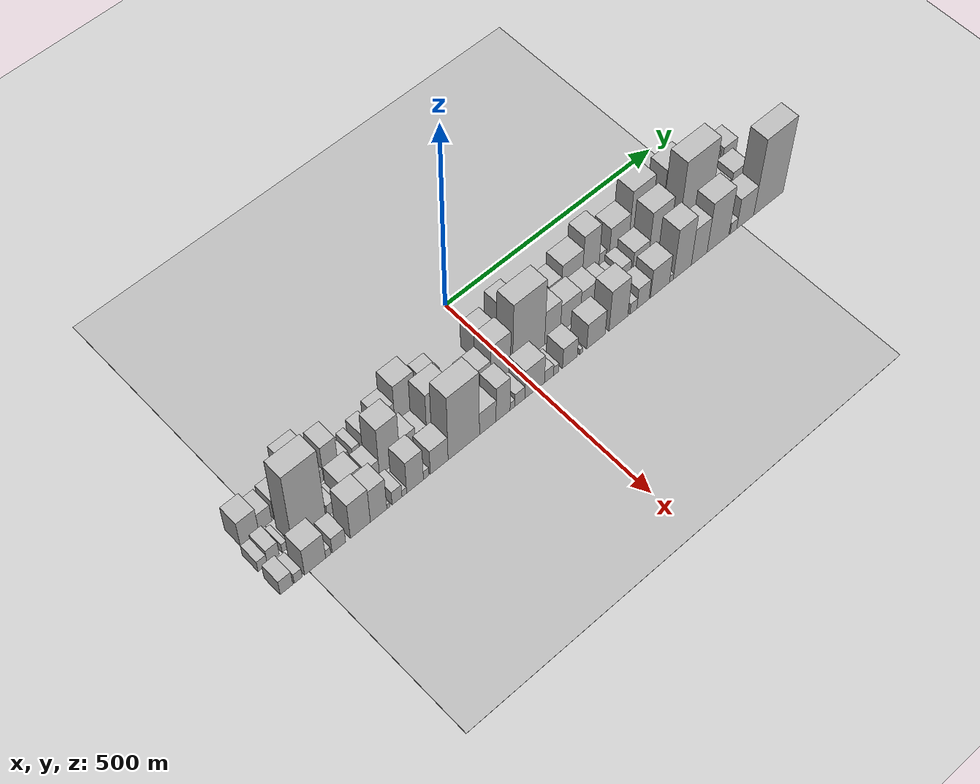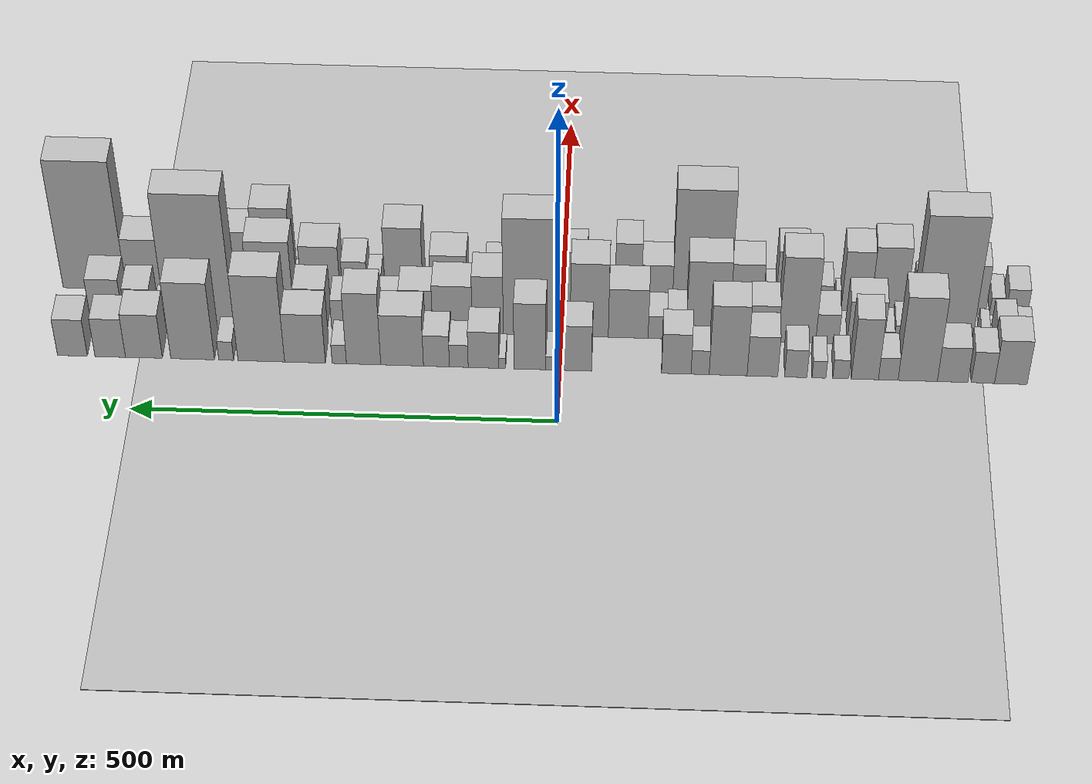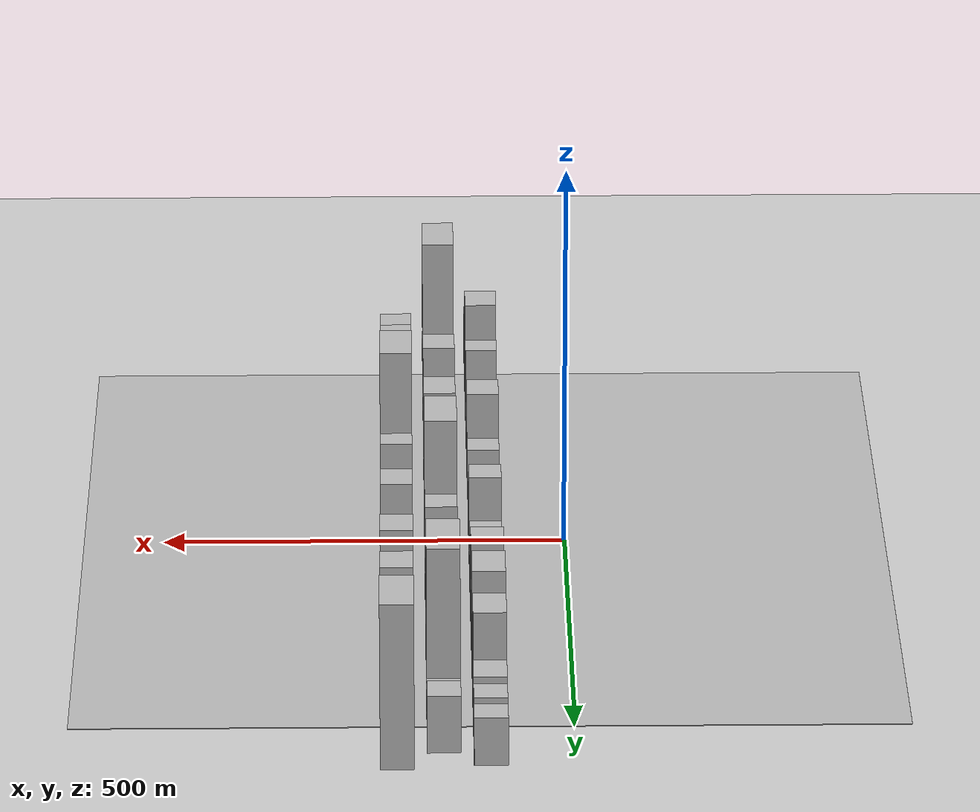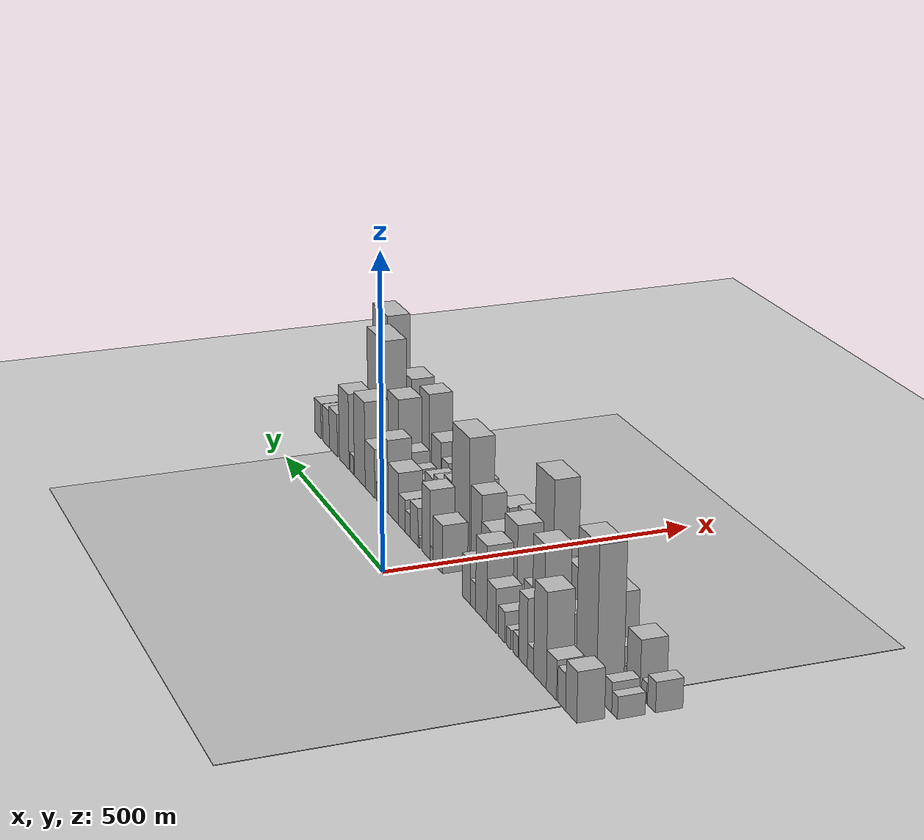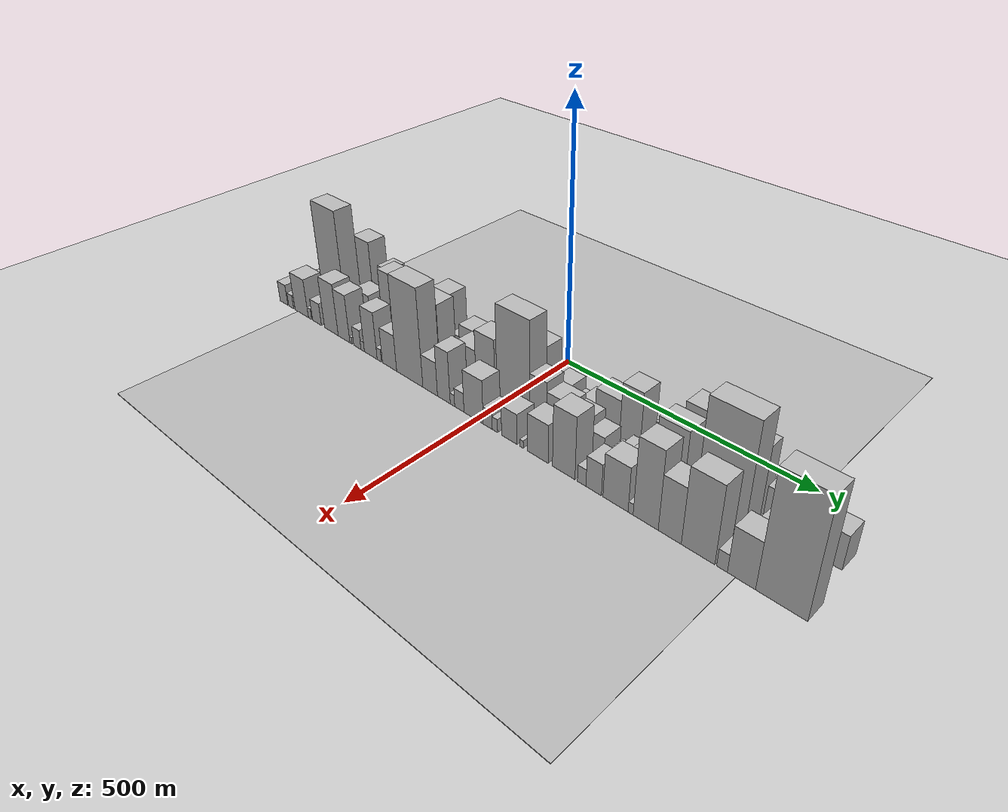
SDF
<?xml version="1.0" encoding="utf-8"?>

<sdf version="1.6">

   <world name="default">

      <gui fullscreen="0">

         <camera name="user_camera">

            <pose>-15 0 4.57585 0 0 0</pose>

            <view_controller>orbit</view_controller>

         </camera>

      </gui>

      <scene>

         <sky>

           <clouds>

             <speed>12</speed>

           </clouds>

         </sky>

         <ambient>0.4 0.4 0.4 1</ambient>

         <background>0.7 0.7 0.7 1</background>

         <shadows>1</shadows>

      </scene>

      <gravity>0 0 -9.8066</gravity>

      <magnetic_field>6e-06 2.3e-05 -4.2e-05</magnetic_field>

      <physics default="0" name="default_physics" type="ode">

         <ode>

            <solver>

               <type>quick</type>

               <iters>10</iters>

               <sor>1.0</sor>

               <use_dynamic_moi_rescaling>0</use_dynamic_moi_rescaling>

            </solver>

            <constraints>

               <cfm>0</cfm>

               <erp>0.2</erp>

               <contact_max_correcting_vel>100</contact_max_correcting_vel>

               <contact_surface_layer>0.001</contact_surface_layer>

            </constraints>

         </ode>

         <max_step_size>0.004</max_step_size>

         <real_time_factor>1</real_time_factor>

         <real_time_update_rate>250</real_time_update_rate>

      </physics>

      <light name="sun" type="directional">

         <cast_shadows>1</cast_shadows>

         <pose>0 0 10 0 0 0</pose>

         <diffuse>0.8 0.8 0.8 1</diffuse>

         <specular>0.2 0.2 0.2 1</specular>

         <attenuation>

            <range>1000</range>

            <constant>0.9</constant>

            <linear>0.01</linear>

            <quadratic>0.001</quadratic>

         </attenuation>

         <direction>-0.5 0.1 -0.9</direction>

      </light>

      <include>

         <name>ground_plane_1</name>

         <uri>model://HANNAS_ground_plane</uri>

         <pose>0 0 0  0 0 0</pose>

      </include>

      <include>

         <name>ground_plane_2</name>

         <uri>model://HANNAS_ground_plane</uri>

         <pose>100 0 0  0 0 0</pose>

      </include>

      <model name="building_1">

         <static>1</static>

         <pose frame="">100.0000 -532.8560 0 0.000000 0.000000 0.000000</pose>

         <link name="link">

            <pose frame="">0 0 37.50 0 0 0</pose>

            <collision name="collision">

               <geometry>

                  <box>

                     <size>40.0000 38.2881 75.0000</size>

                  </box>

               </geometry>

               <max_contacts>10</max_contacts>

               <surface>

                  <contact>

                     <ode/>

                  </contact>

                  <bounce/>

                  <friction>

                     <torsional>

                        <ode/>

                     </torsional>

                     <ode/>

                  </friction>

               </surface>

            </collision>

            <visual name="visual">

               <cast_shadows>0</cast_shadows>

               <geometry>

                  <box>

                     <size>40.0000 38.2881 75.0000</size>

                  </box>

               </geometry>

               <material>

                  <script>

                     <uri>model://HANNAS_wall/materials/scripts</uri>

                     <uri>model://HANNAS_wall/materials/textures</uri>

                     <name>vrc/HANNAS_wall</name>

                  </script>

               </material>

            </visual>

            <self_collide>0</self_collide>

            <enable_wind>0</enable_wind>

            <kinematic>0</kinematic>

         </link>

      </model>

      <model name="building_2">

         <static>1</static>

         <pose frame="">100.0000 -499.9469 0 0.000000 0.000000 0.000000</pose>

         <link name="link">

            <pose frame="">0 0 27.00 0 0 0</pose>

            <collision name="collision">

               <geometry>

                  <box>

                     <size>40.0000 27.5301 54.0000</size>

                  </box>

               </geometry>

               <max_contacts>10</max_contacts>

               <surface>

                  <contact>

                     <ode/>

                  </contact>

                  <bounce/>

                  <friction>

                     <torsional>

                        <ode/>

                     </torsional>

                     <ode/>

                  </friction>

               </surface>

            </collision>

            <visual name="visual">

               <cast_shadows>0</cast_shadows>

               <geometry>

                  <box>

                     <size>40.0000 27.5301 54.0000</size>

                  </box>

               </geometry>

               <material>

                  <script>

                     <uri>model://HANNAS_wall/materials/scripts</uri>

                     <uri>model://HANNAS_wall/materials/textures</uri>

                     <name>vrc/HANNAS_wall</name>

                  </script>

               </material>

            </visual>

            <self_collide>0</self_collide>

            <enable_wind>0</enable_wind>

            <kinematic>0</kinematic>

         </link>

      </model>

      <model name="building_3">

         <static>1</static>

         <pose frame="">100.0000 -464.2220 0 0.000000 0.000000 0.000000</pose>

         <link name="link">

            <pose frame="">0 0 30.00 0 0 0</pose>

            <collision name="collision">

               <geometry>

                  <box>

                     <size>40.0000 35.9197 60.0000</size>

                  </box>

               </geometry>

               <max_contacts>10</max_contacts>

               <surface>

                  <contact>

                     <ode/>

                  </contact>

                  <bounce/>

                  <friction>

                     <torsional>

                        <ode/>

                     </torsional>

                     <ode/>

                  </friction>

               </surface>

            </collision>

            <visual name="visual">

               <cast_shadows>0</cast_shadows>

               <geometry>

                  <box>

                     <size>40.0000 35.9197 60.0000</size>

                  </box>

               </geometry>

               <material>

                  <script>

                     <uri>model://HANNAS_wall/materials/scripts</uri>

                     <uri>model://HANNAS_wall/materials/textures</uri>

                     <name>vrc/HANNAS_wall</name>

                  </script>

               </material>

            </visual>

            <self_collide>0</self_collide>

            <enable_wind>0</enable_wind>

            <kinematic>0</kinematic>

         </link>

      </model>

      <model name="building_4">

         <static>1</static>

         <pose frame="">100.0000 -423.1374 0 0.000000 0.000000 0.000000</pose>

         <link name="link">

            <pose frame="">0 0 72.00 0 0 0</pose>

            <collision name="collision">

               <geometry>

                  <box>

                     <size>40.0000 46.2496 144.0000</size>

                  </box>

               </geometry>

               <max_contacts>10</max_contacts>

               <surface>

                  <contact>

                     <ode/>

                  </contact>

                  <bounce/>

                  <friction>

                     <torsional>

                        <ode/>

                     </torsional>

                     <ode/>

                  </friction>

               </surface>

            </collision>

            <visual name="visual">

               <cast_shadows>0</cast_shadows>

               <geometry>

                  <box>

                     <size>40.0000 46.2496 144.0000</size>

                  </box>

               </geometry>

               <material>

                  <script>

                     <uri>model://HANNAS_wall/materials/scripts</uri>

                     <uri>model://HANNAS_wall/materials/textures</uri>

                     <name>vrc/HANNAS_wall</name>

                  </script>

               </material>

            </visual>

            <self_collide>0</self_collide>

            <enable_wind>0</enable_wind>

            <kinematic>0</kinematic>

         </link>

      </model>

      <model name="building_5">

         <static>1</static>

         <pose frame="">100.0000 -388.4273 0 0.000000 0.000000 0.000000</pose>

         <link name="link">

            <pose frame="">0 0 19.50 0 0 0</pose>

            <collision name="collision">

               <geometry>

                  <box>

                     <size>40.0000 23.1706 39.0000</size>

                  </box>

               </geometry>

               <max_contacts>10</max_contacts>

               <surface>

                  <contact>

                     <ode/>

                  </contact>

                  <bounce/>

                  <friction>

                     <torsional>

                        <ode/>

                     </torsional>

                     <ode/>

                  </friction>

               </surface>

            </collision>

            <visual name="visual">

               <cast_shadows>0</cast_shadows>

               <geometry>

                  <box>

                     <size>40.0000 23.1706 39.0000</size>

                  </box>

               </geometry>

               <material>

                  <script>

                     <uri>model://HANNAS_wall/materials/scripts</uri>

                     <uri>model://HANNAS_wall/materials/textures</uri>

                     <name>vrc/HANNAS_wall</name>

                  </script>

               </material>

            </visual>

            <self_collide>0</self_collide>

            <enable_wind>0</enable_wind>

            <kinematic>0</kinematic>

         </link>

      </model>

      <model name="building_6">

         <static>1</static>

         <pose frame="">100.0000 -360.8542 0 0.000000 0.000000 0.000000</pose>

         <link name="link">

            <pose frame="">0 0 52.50 0 0 0</pose>

            <collision name="collision">

               <geometry>

                  <box>

                     <size>40.0000 31.9754 105.0000</size>

                  </box>

               </geometry>

               <max_contacts>10</max_contacts>

               <surface>

                  <contact>

                     <ode/>

                  </contact>

                  <bounce/>

                  <friction>

                     <torsional>

                        <ode/>

                     </torsional>

                     <ode/>

                  </friction>

               </surface>

            </collision>

            <visual name="visual">

               <cast_shadows>0</cast_shadows>

               <geometry>

                  <box>

                     <size>40.0000 31.9754 105.0000</size>

                  </box>

               </geometry>

               <material>

                  <script>

                     <uri>model://HANNAS_wall/materials/scripts</uri>

                     <uri>model://HANNAS_wall/materials/textures</uri>

                     <name>vrc/HANNAS_wall</name>

                  </script>

               </material>

            </visual>

            <self_collide>0</self_collide>

            <enable_wind>0</enable_wind>

            <kinematic>0</kinematic>

         </link>

      </model>

      <model name="building_7">

         <static>1</static>

         <pose frame="">100.0000 -332.4033 0 0.000000 0.000000 0.000000</pose>

         <link name="link">

            <pose frame="">0 0 16.50 0 0 0</pose>

            <collision name="collision">

               <geometry>

                  <box>

                     <size>40.0000 18.9265 33.0000</size>

                  </box>

               </geometry>

               <max_contacts>10</max_contacts>

               <surface>

                  <contact>

                     <ode/>

                  </contact>

                  <bounce/>

                  <friction>

                     <torsional>

                        <ode/>

                     </torsional>

                     <ode/>

                  </friction>

               </surface>

            </collision>

            <visual name="visual">

               <cast_shadows>0</cast_shadows>

               <geometry>

                  <box>

                     <size>40.0000 18.9265 33.0000</size>

                  </box>

               </geometry>

               <material>

                  <script>

                     <uri>model://HANNAS_wall/materials/scripts</uri>

                     <uri>model://HANNAS_wall/materials/textures</uri>

                     <name>vrc/HANNAS_wall</name>

                  </script>

               </material>

            </visual>

            <self_collide>0</self_collide>

            <enable_wind>0</enable_wind>

            <kinematic>0</kinematic>

         </link>

      </model>

      <model name="building_8">

         <static>1</static>

         <pose frame="">100.0000 -306.7146 0 0.000000 0.000000 0.000000</pose>

         <link name="link">

            <pose frame="">0 0 15.00 0 0 0</pose>

            <collision name="collision">

               <geometry>

                  <box>

                     <size>40.0000 16.4509 30.0000</size>

                  </box>

               </geometry>

               <max_contacts>10</max_contacts>

               <surface>

                  <contact>

                     <ode/>

                  </contact>

                  <bounce/>

                  <friction>

                     <torsional>

                        <ode/>

                     </torsional>

                     <ode/>

                  </friction>

               </surface>

            </collision>

            <visual name="visual">

               <cast_shadows>0</cast_shadows>

               <geometry>

                  <box>

                     <size>40.0000 16.4509 30.0000</size>

                  </box>

               </geometry>

               <material>

                  <script>

                     <uri>model://HANNAS_wall/materials/scripts</uri>

                     <uri>model://HANNAS_wall/materials/textures</uri>

                     <name>vrc/HANNAS_wall</name>

                  </script>

               </material>

            </visual>

            <self_collide>0</self_collide>

            <enable_wind>0</enable_wind>

            <kinematic>0</kinematic>

         </link>

      </model>

      <model name="building_9">

         <static>1</static>

         <pose frame="">100.0000 -279.2729 0 0.000000 0.000000 0.000000</pose>

         <link name="link">

            <pose frame="">0 0 24.00 0 0 0</pose>

            <collision name="collision">

               <geometry>

                  <box>

                     <size>40.0000 26.4324 48.0000</size>

                  </box>

               </geometry>

               <max_contacts>10</max_contacts>

               <surface>

                  <contact>

                     <ode/>

                  </contact>

                  <bounce/>

                  <friction>

                     <torsional>

                        <ode/>

                     </torsional>

                     <ode/>

                  </friction>

               </surface>

            </collision>

            <visual name="visual">

               <cast_shadows>0</cast_shadows>

               <geometry>

                  <box>

                     <size>40.0000 26.4324 48.0000</size>

                  </box>

               </geometry>

               <material>

                  <script>

                     <uri>model://HANNAS_wall/materials/scripts</uri>

                     <uri>model://HANNAS_wall/materials/textures</uri>

                     <name>vrc/HANNAS_wall</name>

                  </script>

               </material>

            </visual>

            <self_collide>0</self_collide>

            <enable_wind>0</enable_wind>

            <kinematic>0</kinematic>

         </link>

      </model>

      <model name="building_10">

         <static>1</static>

         <pose frame="">100.0000 -239.9358 0 0.000000 0.000000 0.000000</pose>

         <link name="link">

            <pose frame="">0 0 34.50 0 0 0</pose>

            <collision name="collision">

               <geometry>

                  <box>

                     <size>40.0000 36.2418 69.0000</size>

                  </box>

               </geometry>

               <max_contacts>10</max_contacts>

               <surface>

                  <contact>

                     <ode/>

                  </contact>

                  <bounce/>

                  <friction>

                     <torsional>

                        <ode/>

                     </torsional>

                     <ode/>

                  </friction>

               </surface>

            </collision>

            <visual name="visual">

               <cast_shadows>0</cast_shadows>

               <geometry>

                  <box>

                     <size>40.0000 36.2418 69.0000</size>

                  </box>

               </geometry>

               <material>

                  <script>

                     <uri>model://HANNAS_wall/materials/scripts</uri>

                     <uri>model://HANNAS_wall/materials/textures</uri>

                     <name>vrc/HANNAS_wall</name>

                  </script>

               </material>

            </visual>

            <self_collide>0</self_collide>

            <enable_wind>0</enable_wind>

            <kinematic>0</kinematic>

         </link>

      </model>

      <model name="building_11">

         <static>1</static>

         <pose frame="">100.0000 -199.3979 0 0.000000 0.000000 0.000000</pose>

         <link name="link">

            <pose frame="">0 0 60.00 0 0 0</pose>

            <collision name="collision">

               <geometry>

                  <box>

                     <size>40.0000 44.8339 120.0000</size>

                  </box>

               </geometry>

               <max_contacts>10</max_contacts>

               <surface>

                  <contact>

                     <ode/>

                  </contact>

                  <bounce/>

                  <friction>

                     <torsional>

                        <ode/>

                     </torsional>

                     <ode/>

                  </friction>

               </surface>

            </collision>

            <visual name="visual">

               <cast_shadows>0</cast_shadows>

               <geometry>

                  <box>

                     <size>40.0000 44.8339 120.0000</size>

                  </box>

               </geometry>

               <material>

                  <script>

                     <uri>model://HANNAS_wall/materials/scripts</uri>

                     <uri>model://HANNAS_wall/materials/textures</uri>

                     <name>vrc/HANNAS_wall</name>

                  </script>

               </material>

            </visual>

            <self_collide>0</self_collide>

            <enable_wind>0</enable_wind>

            <kinematic>0</kinematic>

         </link>

      </model>

      <model name="building_12">

         <static>1</static>

         <pose frame="">100.0000 -166.2604 0 0.000000 0.000000 0.000000</pose>

         <link name="link">

            <pose frame="">0 0 21.00 0 0 0</pose>

            <collision name="collision">

               <geometry>

                  <box>

                     <size>40.0000 21.4410 42.0000</size>

                  </box>

               </geometry>

               <max_contacts>10</max_contacts>

               <surface>

                  <contact>

                     <ode/>

                  </contact>

                  <bounce/>

                  <friction>

                     <torsional>

                        <ode/>

                     </torsional>

                     <ode/>

                  </friction>

               </surface>

            </collision>

            <visual name="visual">

               <cast_shadows>0</cast_shadows>

               <geometry>

                  <box>

                     <size>40.0000 21.4410 42.0000</size>

                  </box>

               </geometry>

               <material>

                  <script>

                     <uri>model://HANNAS_wall/materials/scripts</uri>

                     <uri>model://HANNAS_wall/materials/textures</uri>

                     <name>vrc/HANNAS_wall</name>

                  </script>

               </material>

            </visual>

            <self_collide>0</self_collide>

            <enable_wind>0</enable_wind>

            <kinematic>0</kinematic>

         </link>

      </model>

      <model name="building_13">

         <static>1</static>

         <pose frame="">100.0000 -138.0904 0 0.000000 0.000000 0.000000</pose>

         <link name="link">

            <pose frame="">0 0 34.50 0 0 0</pose>

            <collision name="collision">

               <geometry>

                  <box>

                     <size>40.0000 34.8990 69.0000</size>

                  </box>

               </geometry>

               <max_contacts>10</max_contacts>

               <surface>

                  <contact>

                     <ode/>

                  </contact>

                  <bounce/>

                  <friction>

                     <torsional>

                        <ode/>

                     </torsional>

                     <ode/>

                  </friction>

               </surface>

            </collision>

            <visual name="visual">

               <cast_shadows>0</cast_shadows>

               <geometry>

                  <box>

                     <size>40.0000 34.8990 69.0000</size>

                  </box>

               </geometry>

               <material>

                  <script>

                     <uri>model://HANNAS_wall/materials/scripts</uri>

                     <uri>model://HANNAS_wall/materials/textures</uri>

                     <name>vrc/HANNAS_wall</name>

                  </script>

               </material>

            </visual>

            <self_collide>0</self_collide>

            <enable_wind>0</enable_wind>

            <kinematic>0</kinematic>

         </link>

      </model>

      <model name="building_14">

         <static>1</static>

         <pose frame="">100.0000 -16.3859 0 0.000000 0.000000 0.000000</pose>

         <link name="link">

            <pose frame="">0 0 39.00 0 0 0</pose>

            <collision name="collision">

               <geometry>

                  <box>

                     <size>40.0000 42.8367 78.0000</size>

                  </box>

               </geometry>

               <max_contacts>10</max_contacts>

               <surface>

                  <contact>

                     <ode/>

                  </contact>

                  <bounce/>

                  <friction>

                     <torsional>

                        <ode/>

                     </torsional>

                     <ode/>

                  </friction>

               </surface>

            </collision>

            <visual name="visual">

               <cast_shadows>0</cast_shadows>

               <geometry>

                  <box>

                     <size>40.0000 42.8367 78.0000</size>

                  </box>

               </geometry>

               <material>

                  <script>

                     <uri>model://HANNAS_wall/materials/scripts</uri>

                     <uri>model://HANNAS_wall/materials/textures</uri>

                     <name>vrc/HANNAS_wall</name>

                  </script>

               </material>

            </visual>

            <self_collide>0</self_collide>

            <enable_wind>0</enable_wind>

            <kinematic>0</kinematic>

         </link>

      </model>

      <model name="building_15">

         <static>1</static>

         <pose frame="">100.0000 10.6982 0 0.000000 0.000000 0.000000</pose>

         <link name="link">

            <pose frame="">0 0 12.00 0 0 0</pose>

            <collision name="collision">

               <geometry>

                  <box>

                     <size>40.0000 11.3315 24.0000</size>

                  </box>

               </geometry>

               <max_contacts>10</max_contacts>

               <surface>

                  <contact>

                     <ode/>

                  </contact>

                  <bounce/>

                  <friction>

                     <torsional>

                        <ode/>

                     </torsional>

                     <ode/>

                  </friction>

               </surface>

            </collision>

            <visual name="visual">

               <cast_shadows>0</cast_shadows>

               <geometry>

                  <box>

                     <size>40.0000 11.3315 24.0000</size>

                  </box>

               </geometry>

               <material>

                  <script>

                     <uri>model://HANNAS_wall/materials/scripts</uri>

                     <uri>model://HANNAS_wall/materials/textures</uri>

                     <name>vrc/HANNAS_wall</name>

                  </script>

               </material>

            </visual>

            <self_collide>0</self_collide>

            <enable_wind>0</enable_wind>

            <kinematic>0</kinematic>

         </link>

      </model>

      <model name="building_16">

         <static>1</static>

         <pose frame="">100.0000 35.2625 0 0.000000 0.000000 0.000000</pose>

         <link name="link">

            <pose frame="">0 0 57.00 0 0 0</pose>

            <collision name="collision">

               <geometry>

                  <box>

                     <size>40.0000 37.7971 114.0000</size>

                  </box>

               </geometry>

               <max_contacts>10</max_contacts>

               <surface>

                  <contact>

                     <ode/>

                  </contact>

                  <bounce/>

                  <friction>

                     <torsional>

                        <ode/>

                     </torsional>

                     <ode/>

                  </friction>

               </surface>

            </collision>

            <visual name="visual">

               <cast_shadows>0</cast_shadows>

               <geometry>

                  <box>

                     <size>40.0000 37.7971 114.0000</size>

                  </box>

               </geometry>

               <material>

                  <script>

                     <uri>model://HANNAS_wall/materials/scripts</uri>

                     <uri>model://HANNAS_wall/materials/textures</uri>

                     <name>vrc/HANNAS_wall</name>

                  </script>

               </material>

            </visual>

            <self_collide>0</self_collide>

            <enable_wind>0</enable_wind>

            <kinematic>0</kinematic>

         </link>

      </model>

      <model name="building_17">

         <static>1</static>

         <pose frame="">100.0000 68.1284 0 0.000000 0.000000 0.000000</pose>

         <link name="link">

            <pose frame="">0 0 9.00 0 0 0</pose>

            <collision name="collision">

               <geometry>

                  <box>

                     <size>40.0000 7.9346 18.0000</size>

                  </box>

               </geometry>

               <max_contacts>10</max_contacts>

               <surface>

                  <contact>

                     <ode/>

                  </contact>

                  <bounce/>

                  <friction>

                     <torsional>

                        <ode/>

                     </torsional>

                     <ode/>

                  </friction>

               </surface>

            </collision>

            <visual name="visual">

               <cast_shadows>0</cast_shadows>

               <geometry>

                  <box>

                     <size>40.0000 7.9346 18.0000</size>

                  </box>

               </geometry>

               <material>

                  <script>

                     <uri>model://HANNAS_wall/materials/scripts</uri>

                     <uri>model://HANNAS_wall/materials/textures</uri>

                     <name>vrc/HANNAS_wall</name>

                  </script>

               </material>

            </visual>

            <self_collide>0</self_collide>

            <enable_wind>0</enable_wind>

            <kinematic>0</kinematic>

         </link>

      </model>

      <model name="building_18">

         <static>1</static>

         <pose frame="">100.0000 90.3231 0 0.000000 0.000000 0.000000</pose>

         <link name="link">

            <pose frame="">0 0 31.50 0 0 0</pose>

            <collision name="collision">

               <geometry>

                  <box>

                     <size>40.0000 36.4548 63.0000</size>

                  </box>

               </geometry>

               <max_contacts>10</max_contacts>

               <surface>

                  <contact>

                     <ode/>

                  </contact>

                  <bounce/>

                  <friction>

                     <torsional>

                        <ode/>

                     </torsional>

                     <ode/>

                  </friction>

               </surface>

            </collision>

            <visual name="visual">

               <cast_shadows>0</cast_shadows>

               <geometry>

                  <box>

                     <size>40.0000 36.4548 63.0000</size>

                  </box>

               </geometry>

               <material>

                  <script>

                     <uri>model://HANNAS_wall/materials/scripts</uri>

                     <uri>model://HANNAS_wall/materials/textures</uri>

                     <name>vrc/HANNAS_wall</name>

                  </script>

               </material>

            </visual>

            <self_collide>0</self_collide>

            <enable_wind>0</enable_wind>

            <kinematic>0</kinematic>

         </link>

      </model>

      <model name="building_19">

         <static>1</static>

         <pose frame="">100.0000 119.7356 0 0.000000 0.000000 0.000000</pose>

         <link name="link">

            <pose frame="">0 0 19.50 0 0 0</pose>

            <collision name="collision">

               <geometry>

                  <box>

                     <size>40.0000 22.3701 39.0000</size>

                  </box>

               </geometry>

               <max_contacts>10</max_contacts>

               <surface>

                  <contact>

                     <ode/>

                  </contact>

                  <bounce/>

                  <friction>

                     <torsional>

                        <ode/>

                     </torsional>

                     <ode/>

                  </friction>

               </surface>

            </collision>

            <visual name="visual">

               <cast_shadows>0</cast_shadows>

               <geometry>

                  <box>

                     <size>40.0000 22.3701 39.0000</size>

                  </box>

               </geometry>

               <material>

                  <script>

                     <uri>model://HANNAS_wall/materials/scripts</uri>

                     <uri>model://HANNAS_wall/materials/textures</uri>

                     <name>vrc/HANNAS_wall</name>

                  </script>

               </material>

            </visual>

            <self_collide>0</self_collide>

            <enable_wind>0</enable_wind>

            <kinematic>0</kinematic>

         </link>

      </model>

      <model name="building_20">

         <static>1</static>

         <pose frame="">100.0000 146.3124 0 0.000000 0.000000 0.000000</pose>

         <link name="link">

            <pose frame="">0 0 27.00 0 0 0</pose>

            <collision name="collision">

               <geometry>

                  <box>

                     <size>40.0000 30.7834 54.0000</size>

                  </box>

               </geometry>

               <max_contacts>10</max_contacts>

               <surface>

                  <contact>

                     <ode/>

                  </contact>

                  <bounce/>

                  <friction>

                     <torsional>

                        <ode/>

                     </torsional>

                     <ode/>

                  </friction>

               </surface>

            </collision>

            <visual name="visual">

               <cast_shadows>0</cast_shadows>

               <geometry>

                  <box>

                     <size>40.0000 30.7834 54.0000</size>

                  </box>

               </geometry>

               <material>

                  <script>

                     <uri>model://HANNAS_wall/materials/scripts</uri>

                     <uri>model://HANNAS_wall/materials/textures</uri>

                     <name>vrc/HANNAS_wall</name>

                  </script>

               </material>

            </visual>

            <self_collide>0</self_collide>

            <enable_wind>0</enable_wind>

            <kinematic>0</kinematic>

         </link>

      </model>

      <model name="building_21">

         <static>1</static>

         <pose frame="">100.0000 187.0936 0 0.000000 0.000000 0.000000</pose>

         <link name="link">

            <pose frame="">0 0 43.50 0 0 0</pose>

            <collision name="collision">

               <geometry>

                  <box>

                     <size>40.0000 50.7789 87.0000</size>

                  </box>

               </geometry>

               <max_contacts>10</max_contacts>

               <surface>

                  <contact>

                     <ode/>

                  </contact>

                  <bounce/>

                  <friction>

                     <torsional>

                        <ode/>

                     </torsional>

                     <ode/>

                  </friction>

               </surface>

            </collision>

            <visual name="visual">

               <cast_shadows>0</cast_shadows>

               <geometry>

                  <box>

                     <size>40.0000 50.7789 87.0000</size>

                  </box>

               </geometry>

               <material>

                  <script>

                     <uri>model://HANNAS_wall/materials/scripts</uri>

                     <uri>model://HANNAS_wall/materials/textures</uri>

                     <name>vrc/HANNAS_wall</name>

                  </script>

               </material>

            </visual>

            <self_collide>0</self_collide>

            <enable_wind>0</enable_wind>

            <kinematic>0</kinematic>

         </link>

      </model>

      <model name="building_22">

         <static>1</static>

         <pose frame="">100.0000 232.9016 0 0.000000 0.000000 0.000000</pose>

         <link name="link">

            <pose frame="">0 0 61.50 0 0 0</pose>

            <collision name="collision">

               <geometry>

                  <box>

                     <size>40.0000 40.8372 123.0000</size>

                  </box>

               </geometry>

               <max_contacts>10</max_contacts>

               <surface>

                  <contact>

                     <ode/>

                  </contact>

                  <bounce/>

                  <friction>

                     <torsional>

                        <ode/>

                     </torsional>

                     <ode/>

                  </friction>

               </surface>

            </collision>

            <visual name="visual">

               <cast_shadows>0</cast_shadows>

               <geometry>

                  <box>

                     <size>40.0000 40.8372 123.0000</size>

                  </box>

               </geometry>

               <material>

                  <script>

                     <uri>model://HANNAS_wall/materials/scripts</uri>

                     <uri>model://HANNAS_wall/materials/textures</uri>

                     <name>vrc/HANNAS_wall</name>

                  </script>

               </material>

            </visual>

            <self_collide>0</self_collide>

            <enable_wind>0</enable_wind>

            <kinematic>0</kinematic>

         </link>

      </model>

      <model name="building_23">

         <static>1</static>

         <pose frame="">100.0000 261.8302 0 0.000000 0.000000 0.000000</pose>

         <link name="link">

            <pose frame="">0 0 16.50 0 0 0</pose>

            <collision name="collision">

               <geometry>

                  <box>

                     <size>40.0000 17.0200 33.0000</size>

                  </box>

               </geometry>

               <max_contacts>10</max_contacts>

               <surface>

                  <contact>

                     <ode/>

                  </contact>

                  <bounce/>

                  <friction>

                     <torsional>

                        <ode/>

                     </torsional>

                     <ode/>

                  </friction>

               </surface>

            </collision>

            <visual name="visual">

               <cast_shadows>0</cast_shadows>

               <geometry>

                  <box>

                     <size>40.0000 17.0200 33.0000</size>

                  </box>

               </geometry>

               <material>

                  <script>

                     <uri>model://HANNAS_wall/materials/scripts</uri>

                     <uri>model://HANNAS_wall/materials/textures</uri>

                     <name>vrc/HANNAS_wall</name>

                  </script>

               </material>

            </visual>

            <self_collide>0</self_collide>

            <enable_wind>0</enable_wind>

            <kinematic>0</kinematic>

         </link>

      </model>

      <model name="building_24">

         <static>1</static>

         <pose frame="">100.0000 302.6324 0 0.000000 0.000000 0.000000</pose>

         <link name="link">

            <pose frame="">0 0 42.00 0 0 0</pose>

            <collision name="collision">

               <geometry>

                  <box>

                     <size>40.0000 48.5844 84.0000</size>

                  </box>

               </geometry>

               <max_contacts>10</max_contacts>

               <surface>

                  <contact>

                     <ode/>

                  </contact>

                  <bounce/>

                  <friction>

                     <torsional>

                        <ode/>

                     </torsional>

                     <ode/>

                  </friction>

               </surface>

            </collision>

            <visual name="visual">

               <cast_shadows>0</cast_shadows>

               <geometry>

                  <box>

                     <size>40.0000 48.5844 84.0000</size>

                  </box>

               </geometry>

               <material>

                  <script>

                     <uri>model://HANNAS_wall/materials/scripts</uri>

                     <uri>model://HANNAS_wall/materials/textures</uri>

                     <name>vrc/HANNAS_wall</name>

                  </script>

               </material>

            </visual>

            <self_collide>0</self_collide>

            <enable_wind>0</enable_wind>

            <kinematic>0</kinematic>

         </link>

      </model>

      <model name="building_25">

         <static>1</static>

         <pose frame="">100.0000 354.7784 0 0.000000 0.000000 0.000000</pose>

         <link name="link">

            <pose frame="">0 0 73.50 0 0 0</pose>

            <collision name="collision">

               <geometry>

                  <box>

                     <size>40.0000 55.7074 147.0000</size>

                  </box>

               </geometry>

               <max_contacts>10</max_contacts>

               <surface>

                  <contact>

                     <ode/>

                  </contact>

                  <bounce/>

                  <friction>

                     <torsional>

                        <ode/>

                     </torsional>

                     <ode/>

                  </friction>

               </surface>

            </collision>

            <visual name="visual">

               <cast_shadows>0</cast_shadows>

               <geometry>

                  <box>

                     <size>40.0000 55.7074 147.0000</size>

                  </box>

               </geometry>

               <material>

                  <script>

                     <uri>model://HANNAS_wall/materials/scripts</uri>

                     <uri>model://HANNAS_wall/materials/textures</uri>

                     <name>vrc/HANNAS_wall</name>

                  </script>

               </material>

            </visual>

            <self_collide>0</self_collide>

            <enable_wind>0</enable_wind>

            <kinematic>0</kinematic>

         </link>

      </model>

      <model name="building_26">

         <static>1</static>

         <pose frame="">100.0000 396.5791 0 0.000000 0.000000 0.000000</pose>

         <link name="link">

            <pose frame="">0 0 16.50 0 0 0</pose>

            <collision name="collision">

               <geometry>

                  <box>

                     <size>40.0000 17.8941 33.0000</size>

                  </box>

               </geometry>

               <max_contacts>10</max_contacts>

               <surface>

                  <contact>

                     <ode/>

                  </contact>

                  <bounce/>

                  <friction>

                     <torsional>

                        <ode/>

                     </torsional>

                     <ode/>

                  </friction>

               </surface>

            </collision>

            <visual name="visual">

               <cast_shadows>0</cast_shadows>

               <geometry>

                  <box>

                     <size>40.0000 17.8941 33.0000</size>

                  </box>

               </geometry>

               <material>

                  <script>

                     <uri>model://HANNAS_wall/materials/scripts</uri>

                     <uri>model://HANNAS_wall/materials/textures</uri>

                     <name>vrc/HANNAS_wall</name>

                  </script>

               </material>

            </visual>

            <self_collide>0</self_collide>

            <enable_wind>0</enable_wind>

            <kinematic>0</kinematic>

         </link>

      </model>

      <model name="building_27">

         <static>1</static>

         <pose frame="">100.0000 436.6432 0 0.000000 0.000000 0.000000</pose>

         <link name="link">

            <pose frame="">0 0 66.00 0 0 0</pose>

            <collision name="collision">

               <geometry>

                  <box>

                     <size>40.0000 52.2340 132.0000</size>

                  </box>

               </geometry>

               <max_contacts>10</max_contacts>

               <surface>

                  <contact>

                     <ode/>

                  </contact>

                  <bounce/>

                  <friction>

                     <torsional>

                        <ode/>

                     </torsional>

                     <ode/>

                  </friction>

               </surface>

            </collision>

            <visual name="visual">

               <cast_shadows>0</cast_shadows>

               <geometry>

                  <box>

                     <size>40.0000 52.2340 132.0000</size>

                  </box>

               </geometry>

               <material>

                  <script>

                     <uri>model://HANNAS_wall/materials/scripts</uri>

                     <uri>model://HANNAS_wall/materials/textures</uri>

                     <name>vrc/HANNAS_wall</name>

                  </script>

               </material>

            </visual>

            <self_collide>0</self_collide>

            <enable_wind>0</enable_wind>

            <kinematic>0</kinematic>

         </link>

      </model>

      <model name="building_28">

         <static>1</static>

         <pose frame="">100.0000 494.8409 0 0.000000 0.000000 0.000000</pose>

         <link name="link">

            <pose frame="">0 0 37.50 0 0 0</pose>

            <collision name="collision">

               <geometry>

                  <box>

                     <size>40.0000 44.1613 75.0000</size>

                  </box>

               </geometry>

               <max_contacts>10</max_contacts>

               <surface>

                  <contact>

                     <ode/>

                  </contact>

                  <bounce/>

                  <friction>

                     <torsional>

                        <ode/>

                     </torsional>

                     <ode/>

                  </friction>

               </surface>

            </collision>

            <visual name="visual">

               <cast_shadows>0</cast_shadows>

               <geometry>

                  <box>

                     <size>40.0000 44.1613 75.0000</size>

                  </box>

               </geometry>

               <material>

                  <script>

                     <uri>model://HANNAS_wall/materials/scripts</uri>

                     <uri>model://HANNAS_wall/materials/textures</uri>

                     <name>vrc/HANNAS_wall</name>

                  </script>

               </material>

            </visual>

            <self_collide>0</self_collide>

            <enable_wind>0</enable_wind>

            <kinematic>0</kinematic>

         </link>

      </model>

      <model name="building_29">

         <static>1</static>

         <pose frame="">100.0000 535.1923 0 0.000000 0.000000 0.000000</pose>

         <link name="link">

            <pose frame="">0 0 33.00 0 0 0</pose>

            <collision name="collision">

               <geometry>

                  <box>

                     <size>40.0000 36.5414 66.0000</size>

                  </box>

               </geometry>

               <max_contacts>10</max_contacts>

               <surface>

                  <contact>

                     <ode/>

                  </contact>

                  <bounce/>

                  <friction>

                     <torsional>

                        <ode/>

                     </torsional>

                     <ode/>

                  </friction>

               </surface>

            </collision>

            <visual name="visual">

               <cast_shadows>0</cast_shadows>

               <geometry>

                  <box>

                     <size>40.0000 36.5414 66.0000</size>

                  </box>

               </geometry>

               <material>

                  <script>

                     <uri>model://HANNAS_wall/materials/scripts</uri>

                     <uri>model://HANNAS_wall/materials/textures</uri>

                     <name>vrc/HANNAS_wall</name>

                  </script>

               </material>

            </visual>

            <self_collide>0</self_collide>

            <enable_wind>0</enable_wind>

            <kinematic>0</kinematic>

         </link>

      </model>

      <model name="building_30">

         <static>1</static>

         <pose frame="">100.0000 580.3424 0 0.000000 0.000000 0.000000</pose>

         <link name="link">

            <pose frame="">0 0 31.50 0 0 0</pose>

            <collision name="collision">

               <geometry>

                  <box>

                     <size>40.0000 35.7587 63.0000</size>

                  </box>

               </geometry>

               <max_contacts>10</max_contacts>

               <surface>

                  <contact>

                     <ode/>

                  </contact>

                  <bounce/>

                  <friction>

                     <torsional>

                        <ode/>

                     </torsional>

                     <ode/>

                  </friction>

               </surface>

            </collision>

            <visual name="visual">

               <cast_shadows>0</cast_shadows>

               <geometry>

                  <box>

                     <size>40.0000 35.7587 63.0000</size>

                  </box>

               </geometry>

               <material>

                  <script>

                     <uri>model://HANNAS_wall/materials/scripts</uri>

                     <uri>model://HANNAS_wall/materials/textures</uri>

                     <name>vrc/HANNAS_wall</name>

                  </script>

               </material>

            </visual>

            <self_collide>0</self_collide>

            <enable_wind>0</enable_wind>

            <kinematic>0</kinematic>

         </link>

      </model>

      <model name="building_31">

         <static>1</static>

         <pose frame="">155.0000 -550.4617 0 0.000000 0.000000 0.000000</pose>

         <link name="link">

            <pose frame="">0 0 16.50 0 0 0</pose>

            <collision name="collision">

               <geometry>

                  <box>

                     <size>40.0000 19.0766 33.0000</size>

                  </box>

               </geometry>

               <max_contacts>10</max_contacts>

               <surface>

                  <contact>

                     <ode/>

                  </contact>

                  <bounce/>

                  <friction>

                     <torsional>

                        <ode/>

                     </torsional>

                     <ode/>

                  </friction>

               </surface>

            </collision>

            <visual name="visual">

               <cast_shadows>0</cast_shadows>

               <geometry>

                  <box>

                     <size>40.0000 19.0766 33.0000</size>

                  </box>

               </geometry>

               <material>

                  <script>

                     <uri>model://HANNAS_wall/materials/scripts</uri>

                     <uri>model://HANNAS_wall/materials/textures</uri>

                     <name>vrc/HANNAS_wall</name>

                  </script>

               </material>

            </visual>

            <self_collide>0</self_collide>

            <enable_wind>0</enable_wind>

            <kinematic>0</kinematic>

         </link>

      </model>

      <model name="building_32">

         <static>1</static>

         <pose frame="">155.0000 -528.6336 0 0.000000 0.000000 0.000000</pose>

         <link name="link">

            <pose frame="">0 0 22.50 0 0 0</pose>

            <collision name="collision">

               <geometry>

                  <box>

                     <size>40.0000 24.5795 45.0000</size>

                  </box>

               </geometry>

               <max_contacts>10</max_contacts>

               <surface>

                  <contact>

                     <ode/>

                  </contact>

                  <bounce/>

                  <friction>

                     <torsional>

                        <ode/>

                     </torsional>

                     <ode/>

                  </friction>

               </surface>

            </collision>

            <visual name="visual">

               <cast_shadows>0</cast_shadows>

               <geometry>

                  <box>

                     <size>40.0000 24.5795 45.0000</size>

                  </box>

               </geometry>

               <material>

                  <script>

                     <uri>model://HANNAS_wall/materials/scripts</uri>

                     <uri>model://HANNAS_wall/materials/textures</uri>

                     <name>vrc/HANNAS_wall</name>

                  </script>

               </material>

            </visual>

            <self_collide>0</self_collide>

            <enable_wind>0</enable_wind>

            <kinematic>0</kinematic>

         </link>

      </model>

      <model name="building_33">

         <static>1</static>

         <pose frame="">155.0000 -504.8861 0 0.000000 0.000000 0.000000</pose>

         <link name="link">

            <pose frame="">0 0 13.50 0 0 0</pose>

            <collision name="collision">

               <geometry>

                  <box>

                     <size>40.0000 10.9157 27.0000</size>

                  </box>

               </geometry>

               <max_contacts>10</max_contacts>

               <surface>

                  <contact>

                     <ode/>

                  </contact>

                  <bounce/>

                  <friction>

                     <torsional>

                        <ode/>

                     </torsional>

                     <ode/>

                  </friction>

               </surface>

            </collision>

            <visual name="visual">

               <cast_shadows>0</cast_shadows>

               <geometry>

                  <box>

                     <size>40.0000 10.9157 27.0000</size>

                  </box>

               </geometry>

               <material>

                  <script>

                     <uri>model://HANNAS_wall/materials/scripts</uri>

                     <uri>model://HANNAS_wall/materials/textures</uri>

                     <name>vrc/HANNAS_wall</name>

                  </script>

               </material>

            </visual>

            <self_collide>0</self_collide>

            <enable_wind>0</enable_wind>

            <kinematic>0</kinematic>

         </link>

      </model>

      <model name="building_34">

         <static>1</static>

         <pose frame="">155.0000 -454.1175 0 0.000000 0.000000 0.000000</pose>

         <link name="link">

            <pose frame="">0 0 111.00 0 0 0</pose>

            <collision name="collision">

               <geometry>

                  <box>

                     <size>40.0000 70.6215 222.0000</size>

                  </box>

               </geometry>

               <max_contacts>10</max_contacts>

               <surface>

                  <contact>

                     <ode/>

                  </contact>

                  <bounce/>

                  <friction>

                     <torsional>

                        <ode/>

                     </torsional>

                     <ode/>

                  </friction>

               </surface>

            </collision>

            <visual name="visual">

               <cast_shadows>0</cast_shadows>

               <geometry>

                  <box>

                     <size>40.0000 70.6215 222.0000</size>

                  </box>

               </geometry>

               <material>

                  <script>

                     <uri>model://HANNAS_wall/materials/scripts</uri>

                     <uri>model://HANNAS_wall/materials/textures</uri>

                     <name>vrc/HANNAS_wall</name>

                  </script>

               </material>

            </visual>

            <self_collide>0</self_collide>

            <enable_wind>0</enable_wind>

            <kinematic>0</kinematic>

         </link>

      </model>

      <model name="building_35">

         <static>1</static>

         <pose frame="">155.0000 -406.4657 0 0.000000 0.000000 0.000000</pose>

         <link name="link">

            <pose frame="">0 0 18.00 0 0 0</pose>

            <collision name="collision">

               <geometry>

                  <box>

                     <size>40.0000 18.6821 36.0000</size>

                  </box>

               </geometry>

               <max_contacts>10</max_contacts>

               <surface>

                  <contact>

                     <ode/>

                  </contact>

                  <bounce/>

                  <friction>

                     <torsional>

                        <ode/>

                     </torsional>

                     <ode/>

                  </friction>

               </surface>

            </collision>

            <visual name="visual">

               <cast_shadows>0</cast_shadows>

               <geometry>

                  <box>

                     <size>40.0000 18.6821 36.0000</size>

                  </box>

               </geometry>

               <material>

                  <script>

                     <uri>model://HANNAS_wall/materials/scripts</uri>

                     <uri>model://HANNAS_wall/materials/textures</uri>

                     <name>vrc/HANNAS_wall</name>

                  </script>

               </material>

            </visual>

            <self_collide>0</self_collide>

            <enable_wind>0</enable_wind>

            <kinematic>0</kinematic>

         </link>

      </model>

      <model name="building_36">

         <static>1</static>

         <pose frame="">155.0000 -391.2369 0 0.000000 0.000000 0.000000</pose>

         <link name="link">

            <pose frame="">0 0 12.00 0 0 0</pose>

            <collision name="collision">

               <geometry>

                  <box>

                     <size>40.0000 11.7754 24.0000</size>

                  </box>

               </geometry>

               <max_contacts>10</max_contacts>

               <surface>

                  <contact>

                     <ode/>

                  </contact>

                  <bounce/>

                  <friction>

                     <torsional>

                        <ode/>

                     </torsional>

                     <ode/>

                  </friction>

               </surface>

            </collision>

            <visual name="visual">

               <cast_shadows>0</cast_shadows>

               <geometry>

                  <box>

                     <size>40.0000 11.7754 24.0000</size>

                  </box>

               </geometry>

               <material>

                  <script>

                     <uri>model://HANNAS_wall/materials/scripts</uri>

                     <uri>model://HANNAS_wall/materials/textures</uri>

                     <name>vrc/HANNAS_wall</name>

                  </script>

               </material>

            </visual>

            <self_collide>0</self_collide>

            <enable_wind>0</enable_wind>

            <kinematic>0</kinematic>

         </link>

      </model>

      <model name="building_37">

         <static>1</static>

         <pose frame="">155.0000 -363.3396 0 0.000000 0.000000 0.000000</pose>

         <link name="link">

            <pose frame="">0 0 37.50 0 0 0</pose>

            <collision name="collision">

               <geometry>

                  <box>

                     <size>40.0000 44.0192 75.0000</size>

                  </box>

               </geometry>

               <max_contacts>10</max_contacts>

               <surface>

                  <contact>

                     <ode/>

                  </contact>

                  <bounce/>

                  <friction>

                     <torsional>

                        <ode/>

                     </torsional>

                     <ode/>

                  </friction>

               </surface>

            </collision>

            <visual name="visual">

               <cast_shadows>0</cast_shadows>

               <geometry>

                  <box>

                     <size>40.0000 44.0192 75.0000</size>

                  </box>

               </geometry>

               <material>

                  <script>

                     <uri>model://HANNAS_wall/materials/scripts</uri>

                     <uri>model://HANNAS_wall/materials/textures</uri>

                     <name>vrc/HANNAS_wall</name>

                  </script>

               </material>

            </visual>

            <self_collide>0</self_collide>

            <enable_wind>0</enable_wind>

            <kinematic>0</kinematic>

         </link>

      </model>

      <model name="building_38">

         <static>1</static>

         <pose frame="">155.0000 -317.6181 0 0.000000 0.000000 0.000000</pose>

         <link name="link">

            <pose frame="">0 0 25.50 0 0 0</pose>

            <collision name="collision">

               <geometry>

                  <box>

                     <size>40.0000 27.4237 51.0000</size>

                  </box>

               </geometry>

               <max_contacts>10</max_contacts>

               <surface>

                  <contact>

                     <ode/>

                  </contact>

                  <bounce/>

                  <friction>

                     <torsional>

                        <ode/>

                     </torsional>

                     <ode/>

                  </friction>

               </surface>

            </collision>

            <visual name="visual">

               <cast_shadows>0</cast_shadows>

               <geometry>

                  <box>

                     <size>40.0000 27.4237 51.0000</size>

                  </box>

               </geometry>

               <material>

                  <script>

                     <uri>model://HANNAS_wall/materials/scripts</uri>

                     <uri>model://HANNAS_wall/materials/textures</uri>

                     <name>vrc/HANNAS_wall</name>

                  </script>

               </material>

            </visual>

            <self_collide>0</self_collide>

            <enable_wind>0</enable_wind>

            <kinematic>0</kinematic>

         </link>

      </model>

      <model name="building_39">

         <static>1</static>

         <pose frame="">155.0000 -281.6502 0 0.000000 0.000000 0.000000</pose>

         <link name="link">

            <pose frame="">0 0 73.50 0 0 0</pose>

            <collision name="collision">

               <geometry>

                  <box>

                     <size>40.0000 44.5122 147.0000</size>

                  </box>

               </geometry>

               <max_contacts>10</max_contacts>

               <surface>

                  <contact>

                     <ode/>

                  </contact>

                  <bounce/>

                  <friction>

                     <torsional>

                        <ode/>

                     </torsional>

                     <ode/>

                  </friction>

               </surface>

            </collision>

            <visual name="visual">

               <cast_shadows>0</cast_shadows>

               <geometry>

                  <box>

                     <size>40.0000 44.5122 147.0000</size>

                  </box>

               </geometry>

               <material>

                  <script>

                     <uri>model://HANNAS_wall/materials/scripts</uri>

                     <uri>model://HANNAS_wall/materials/textures</uri>

                     <name>vrc/HANNAS_wall</name>

                  </script>

               </material>

            </visual>

            <self_collide>0</self_collide>

            <enable_wind>0</enable_wind>

            <kinematic>0</kinematic>

         </link>

      </model>

      <model name="building_40">

         <static>1</static>

         <pose frame="">155.0000 -242.1635 0 0.000000 0.000000 0.000000</pose>

         <link name="link">

            <pose frame="">0 0 31.50 0 0 0</pose>

            <collision name="collision">

               <geometry>

                  <box>

                     <size>40.0000 34.4611 63.0000</size>

                  </box>

               </geometry>

               <max_contacts>10</max_contacts>

               <surface>

                  <contact>

                     <ode/>

                  </contact>

                  <bounce/>

                  <friction>

                     <torsional>

                        <ode/>

                     </torsional>

                     <ode/>

                  </friction>

               </surface>

            </collision>

            <visual name="visual">

               <cast_shadows>0</cast_shadows>

               <geometry>

                  <box>

                     <size>40.0000 34.4611 63.0000</size>

                  </box>

               </geometry>

               <material>

                  <script>

                     <uri>model://HANNAS_wall/materials/scripts</uri>

                     <uri>model://HANNAS_wall/materials/textures</uri>

                     <name>vrc/HANNAS_wall</name>

                  </script>

               </material>

            </visual>

            <self_collide>0</self_collide>

            <enable_wind>0</enable_wind>

            <kinematic>0</kinematic>

         </link>

      </model>

      <model name="building_41">

         <static>1</static>

         <pose frame="">155.0000 -212.4533 0 0.000000 0.000000 0.000000</pose>

         <link name="link">

            <pose frame="">0 0 21.00 0 0 0</pose>

            <collision name="collision">

               <geometry>

                  <box>

                     <size>40.0000 24.9593 42.0000</size>

                  </box>

               </geometry>

               <max_contacts>10</max_contacts>

               <surface>

                  <contact>

                     <ode/>

                  </contact>

                  <bounce/>

                  <friction>

                     <torsional>

                        <ode/>

                     </torsional>

                     <ode/>

                  </friction>

               </surface>

            </collision>

            <visual name="visual">

               <cast_shadows>0</cast_shadows>

               <geometry>

                  <box>

                     <size>40.0000 24.9593 42.0000</size>

                  </box>

               </geometry>

               <material>

                  <script>

                     <uri>model://HANNAS_wall/materials/scripts</uri>

                     <uri>model://HANNAS_wall/materials/textures</uri>

                     <name>vrc/HANNAS_wall</name>

                  </script>

               </material>

            </visual>

            <self_collide>0</self_collide>

            <enable_wind>0</enable_wind>

            <kinematic>0</kinematic>

         </link>

      </model>

      <model name="building_42">

         <static>1</static>

         <pose frame="">155.0000 -174.4409 0 0.000000 0.000000 0.000000</pose>

         <link name="link">

            <pose frame="">0 0 67.50 0 0 0</pose>

            <collision name="collision">

               <geometry>

                  <box>

                     <size>40.0000 51.0656 135.0000</size>

                  </box>

               </geometry>

               <max_contacts>10</max_contacts>

               <surface>

                  <contact>

                     <ode/>

                  </contact>

                  <bounce/>

                  <friction>

                     <torsional>

                        <ode/>

                     </torsional>

                     <ode/>

                  </friction>

               </surface>

            </collision>

            <visual name="visual">

               <cast_shadows>0</cast_shadows>

               <geometry>

                  <box>

                     <size>40.0000 51.0656 135.0000</size>

                  </box>

               </geometry>

               <material>

                  <script>

                     <uri>model://HANNAS_wall/materials/scripts</uri>

                     <uri>model://HANNAS_wall/materials/textures</uri>

                     <name>vrc/HANNAS_wall</name>

                  </script>

               </material>

            </visual>

            <self_collide>0</self_collide>

            <enable_wind>0</enable_wind>

            <kinematic>0</kinematic>

         </link>

      </model>

      <model name="building_43">

         <static>1</static>

         <pose frame="">155.0000 -137.5080 0 0.000000 0.000000 0.000000</pose>

         <link name="link">

            <pose frame="">0 0 22.50 0 0 0</pose>

            <collision name="collision">

               <geometry>

                  <box>

                     <size>40.0000 22.8001 45.0000</size>

                  </box>

               </geometry>

               <max_contacts>10</max_contacts>

               <surface>

                  <contact>

                     <ode/>

                  </contact>

                  <bounce/>

                  <friction>

                     <torsional>

                        <ode/>

                     </torsional>

                     <ode/>

                  </friction>

               </surface>

            </collision>

            <visual name="visual">

               <cast_shadows>0</cast_shadows>

               <geometry>

                  <box>

                     <size>40.0000 22.8001 45.0000</size>

                  </box>

               </geometry>

               <material>

                  <script>

                     <uri>model://HANNAS_wall/materials/scripts</uri>

                     <uri>model://HANNAS_wall/materials/textures</uri>

                     <name>vrc/HANNAS_wall</name>

                  </script>

               </material>

            </visual>

            <self_collide>0</self_collide>

            <enable_wind>0</enable_wind>

            <kinematic>0</kinematic>

         </link>

      </model>

      <model name="building_44">

         <static>1</static>

         <pose frame="">155.0000 -114.9697 0 0.000000 0.000000 0.000000</pose>

         <link name="link">

            <pose frame="">0 0 19.50 0 0 0</pose>

            <collision name="collision">

               <geometry>

                  <box>

                     <size>40.0000 22.2766 39.0000</size>

                  </box>

               </geometry>

               <max_contacts>10</max_contacts>

               <surface>

                  <contact>

                     <ode/>

                  </contact>

                  <bounce/>

                  <friction>

                     <torsional>

                        <ode/>

                     </torsional>

                     <ode/>

                  </friction>

               </surface>

            </collision>

            <visual name="visual">

               <cast_shadows>0</cast_shadows>

               <geometry>

                  <box>

                     <size>40.0000 22.2766 39.0000</size>

                  </box>

               </geometry>

               <material>

                  <script>

                     <uri>model://HANNAS_wall/materials/scripts</uri>

                     <uri>model://HANNAS_wall/materials/textures</uri>

                     <name>vrc/HANNAS_wall</name>

                  </script>

               </material>

            </visual>

            <self_collide>0</self_collide>

            <enable_wind>0</enable_wind>

            <kinematic>0</kinematic>

         </link>

      </model>

      <model name="building_45">

         <static>1</static>

         <pose frame="">155.0000 -80.0191 0 0.000000 0.000000 0.000000</pose>

         <link name="link">

            <pose frame="">0 0 42.00 0 0 0</pose>

            <collision name="collision">

               <geometry>

                  <box>

                     <size>40.0000 47.6246 84.0000</size>

                  </box>

               </geometry>

               <max_contacts>10</max_contacts>

               <surface>

                  <contact>

                     <ode/>

                  </contact>

                  <bounce/>

                  <friction>

                     <torsional>

                        <ode/>

                     </torsional>

                     <ode/>

                  </friction>

               </surface>

            </collision>

            <visual name="visual">

               <cast_shadows>0</cast_shadows>

               <geometry>

                  <box>

                     <size>40.0000 47.6246 84.0000</size>

                  </box>

               </geometry>

               <material>

                  <script>

                     <uri>model://HANNAS_wall/materials/scripts</uri>

                     <uri>model://HANNAS_wall/materials/textures</uri>

                     <name>vrc/HANNAS_wall</name>

                  </script>

               </material>

            </visual>

            <self_collide>0</self_collide>

            <enable_wind>0</enable_wind>

            <kinematic>0</kinematic>

         </link>

      </model>

      <model name="building_46">

         <static>1</static>

         <pose frame="">155.0000 -33.4215 0 0.000000 0.000000 0.000000</pose>

         <link name="link">

            <pose frame="">0 0 63.00 0 0 0</pose>

            <collision name="collision">

               <geometry>

                  <box>

                     <size>40.0000 45.5707 126.0000</size>

                  </box>

               </geometry>

               <max_contacts>10</max_contacts>

               <surface>

                  <contact>

                     <ode/>

                  </contact>

                  <bounce/>

                  <friction>

                     <torsional>

                        <ode/>

                     </torsional>

                     <ode/>

                  </friction>

               </surface>

            </collision>

            <visual name="visual">

               <cast_shadows>0</cast_shadows>

               <geometry>

                  <box>

                     <size>40.0000 45.5707 126.0000</size>

                  </box>

               </geometry>

               <material>

                  <script>

                     <uri>model://HANNAS_wall/materials/scripts</uri>

                     <uri>model://HANNAS_wall/materials/textures</uri>

                     <name>vrc/HANNAS_wall</name>

                  </script>

               </material>

            </visual>

            <self_collide>0</self_collide>

            <enable_wind>0</enable_wind>

            <kinematic>0</kinematic>

         </link>

      </model>

      <model name="building_47">

         <static>1</static>

         <pose frame="">155.0000 31.9254 0 0.000000 0.000000 0.000000</pose>

         <link name="link">

            <pose frame="">0 0 99.00 0 0 0</pose>

            <collision name="collision">

               <geometry>

                  <box>

                     <size>40.0000 75.1230 198.0000</size>

                  </box>

               </geometry>

               <max_contacts>10</max_contacts>

               <surface>

                  <contact>

                     <ode/>

                  </contact>

                  <bounce/>

                  <friction>

                     <torsional>

                        <ode/>

                     </torsional>

                     <ode/>

                  </friction>

               </surface>

            </collision>

            <visual name="visual">

               <cast_shadows>0</cast_shadows>

               <geometry>

                  <box>

                     <size>40.0000 75.1230 198.0000</size>

                  </box>

               </geometry>

               <material>

                  <script>

                     <uri>model://HANNAS_wall/materials/scripts</uri>

                     <uri>model://HANNAS_wall/materials/textures</uri>

                     <name>vrc/HANNAS_wall</name>

                  </script>

               </material>

            </visual>

            <self_collide>0</self_collide>

            <enable_wind>0</enable_wind>

            <kinematic>0</kinematic>

         </link>

      </model>

      <model name="building_48">

         <static>1</static>

         <pose frame="">155.0000 88.0605 0 0.000000 0.000000 0.000000</pose>

         <link name="link">

            <pose frame="">0 0 49.50 0 0 0</pose>

            <collision name="collision">

               <geometry>

                  <box>

                     <size>40.0000 37.1473 99.0000</size>

                  </box>

               </geometry>

               <max_contacts>10</max_contacts>

               <surface>

                  <contact>

                     <ode/>

                  </contact>

                  <bounce/>

                  <friction>

                     <torsional>

                        <ode/>

                     </torsional>

                     <ode/>

                  </friction>

               </surface>

            </collision>

            <visual name="visual">

               <cast_shadows>0</cast_shadows>

               <geometry>

                  <box>

                     <size>40.0000 37.1473 99.0000</size>

                  </box>

               </geometry>

               <material>

                  <script>

                     <uri>model://HANNAS_wall/materials/scripts</uri>

                     <uri>model://HANNAS_wall/materials/textures</uri>

                     <name>vrc/HANNAS_wall</name>

                  </script>

               </material>

            </visual>

            <self_collide>0</self_collide>

            <enable_wind>0</enable_wind>

            <kinematic>0</kinematic>

         </link>

      </model>

      <model name="building_49">

         <static>1</static>

         <pose frame="">155.0000 130.4481 0 0.000000 0.000000 0.000000</pose>

         <link name="link">

            <pose frame="">0 0 40.50 0 0 0</pose>

            <collision name="collision">

               <geometry>

                  <box>

                     <size>40.0000 47.6279 81.0000</size>

                  </box>

               </geometry>

               <max_contacts>10</max_contacts>

               <surface>

                  <contact>

                     <ode/>

                  </contact>

                  <bounce/>

                  <friction>

                     <torsional>

                        <ode/>

                     </torsional>

                     <ode/>

                  </friction>

               </surface>

            </collision>

            <visual name="visual">

               <cast_shadows>0</cast_shadows>

               <geometry>

                  <box>

                     <size>40.0000 47.6279 81.0000</size>

                  </box>

               </geometry>

               <material>

                  <script>

                     <uri>model://HANNAS_wall/materials/scripts</uri>

                     <uri>model://HANNAS_wall/materials/textures</uri>

                     <name>vrc/HANNAS_wall</name>

                  </script>

               </material>

            </visual>

            <self_collide>0</self_collide>

            <enable_wind>0</enable_wind>

            <kinematic>0</kinematic>

         </link>

      </model>

      <model name="building_50">

         <static>1</static>

         <pose frame="">155.0000 174.0246 0 0.000000 0.000000 0.000000</pose>

         <link name="link">

            <pose frame="">0 0 36.00 0 0 0</pose>

            <collision name="collision">

               <geometry>

                  <box>

                     <size>40.0000 39.5250 72.0000</size>

                  </box>

               </geometry>

               <max_contacts>10</max_contacts>

               <surface>

                  <contact>

                     <ode/>

                  </contact>

                  <bounce/>

                  <friction>

                     <torsional>

                        <ode/>

                     </torsional>

                     <ode/>

                  </friction>

               </surface>

            </collision>

            <visual name="visual">

               <cast_shadows>0</cast_shadows>

               <geometry>

                  <box>

                     <size>40.0000 39.5250 72.0000</size>

                  </box>

               </geometry>

               <material>

                  <script>

                     <uri>model://HANNAS_wall/materials/scripts</uri>

                     <uri>model://HANNAS_wall/materials/textures</uri>

                     <name>vrc/HANNAS_wall</name>

                  </script>

               </material>

            </visual>

            <self_collide>0</self_collide>

            <enable_wind>0</enable_wind>

            <kinematic>0</kinematic>

         </link>

      </model>

      <model name="building_51">

         <static>1</static>

         <pose frame="">155.0000 209.7102 0 0.000000 0.000000 0.000000</pose>

         <link name="link">

            <pose frame="">0 0 27.00 0 0 0</pose>

            <collision name="collision">

               <geometry>

                  <box>

                     <size>40.0000 31.8461 54.0000</size>

                  </box>

               </geometry>

               <max_contacts>10</max_contacts>

               <surface>

                  <contact>

                     <ode/>

                  </contact>

                  <bounce/>

                  <friction>

                     <torsional>

                        <ode/>

                     </torsional>

                     <ode/>

                  </friction>

               </surface>

            </collision>

            <visual name="visual">

               <cast_shadows>0</cast_shadows>

               <geometry>

                  <box>

                     <size>40.0000 31.8461 54.0000</size>

                  </box>

               </geometry>

               <material>

                  <script>

                     <uri>model://HANNAS_wall/materials/scripts</uri>

                     <uri>model://HANNAS_wall/materials/textures</uri>

                     <name>vrc/HANNAS_wall</name>

                  </script>

               </material>

            </visual>

            <self_collide>0</self_collide>

            <enable_wind>0</enable_wind>

            <kinematic>0</kinematic>

         </link>

      </model>

      <model name="building_52">

         <static>1</static>

         <pose frame="">155.0000 240.8804 0 0.000000 0.000000 0.000000</pose>

         <link name="link">

            <pose frame="">0 0 16.50 0 0 0</pose>

            <collision name="collision">

               <geometry>

                  <box>

                     <size>40.0000 18.4943 33.0000</size>

                  </box>

               </geometry>

               <max_contacts>10</max_contacts>

               <surface>

                  <contact>

                     <ode/>

                  </contact>

                  <bounce/>

                  <friction>

                     <torsional>

                        <ode/>

                     </torsional>

                     <ode/>

                  </friction>

               </surface>

            </collision>

            <visual name="visual">

               <cast_shadows>0</cast_shadows>

               <geometry>

                  <box>

                     <size>40.0000 18.4943 33.0000</size>

                  </box>

               </geometry>

               <material>

                  <script>

                     <uri>model://HANNAS_wall/materials/scripts</uri>

                     <uri>model://HANNAS_wall/materials/textures</uri>

                     <name>vrc/HANNAS_wall</name>

                  </script>

               </material>

            </visual>

            <self_collide>0</self_collide>

            <enable_wind>0</enable_wind>

            <kinematic>0</kinematic>

         </link>

      </model>

      <model name="building_53">

         <static>1</static>

         <pose frame="">155.0000 262.9508 0 0.000000 0.000000 0.000000</pose>

         <link name="link">

            <pose frame="">0 0 25.50 0 0 0</pose>

            <collision name="collision">

               <geometry>

                  <box>

                     <size>40.0000 25.6466 51.0000</size>

                  </box>

               </geometry>

               <max_contacts>10</max_contacts>

               <surface>

                  <contact>

                     <ode/>

                  </contact>

                  <bounce/>

                  <friction>

                     <torsional>

                        <ode/>

                     </torsional>

                     <ode/>

                  </friction>

               </surface>

            </collision>

            <visual name="visual">

               <cast_shadows>0</cast_shadows>

               <geometry>

                  <box>

                     <size>40.0000 25.6466 51.0000</size>

                  </box>

               </geometry>

               <material>

                  <script>

                     <uri>model://HANNAS_wall/materials/scripts</uri>

                     <uri>model://HANNAS_wall/materials/textures</uri>

                     <name>vrc/HANNAS_wall</name>

                  </script>

               </material>

            </visual>

            <self_collide>0</self_collide>

            <enable_wind>0</enable_wind>

            <kinematic>0</kinematic>

         </link>

      </model>

      <model name="building_54">

         <static>1</static>

         <pose frame="">155.0000 300.0967 0 0.000000 0.000000 0.000000</pose>

         <link name="link">

            <pose frame="">0 0 34.50 0 0 0</pose>

            <collision name="collision">

               <geometry>

                  <box>

                     <size>40.0000 38.6452 69.0000</size>

                  </box>

               </geometry>

               <max_contacts>10</max_contacts>

               <surface>

                  <contact>

                     <ode/>

                  </contact>

                  <bounce/>

                  <friction>

                     <torsional>

                        <ode/>

                     </torsional>

                     <ode/>

                  </friction>

               </surface>

            </collision>

            <visual name="visual">

               <cast_shadows>0</cast_shadows>

               <geometry>

                  <box>

                     <size>40.0000 38.6452 69.0000</size>

                  </box>

               </geometry>

               <material>

                  <script>

                     <uri>model://HANNAS_wall/materials/scripts</uri>

                     <uri>model://HANNAS_wall/materials/textures</uri>

                     <name>vrc/HANNAS_wall</name>

                  </script>

               </material>

            </visual>

            <self_collide>0</self_collide>

            <enable_wind>0</enable_wind>

            <kinematic>0</kinematic>

         </link>

      </model>

      <model name="building_55">

         <static>1</static>

         <pose frame="">155.0000 345.8321 0 0.000000 0.000000 0.000000</pose>

         <link name="link">

            <pose frame="">0 0 73.50 0 0 0</pose>

            <collision name="collision">

               <geometry>

                  <box>

                     <size>40.0000 52.8255 147.0000</size>

                  </box>

               </geometry>

               <max_contacts>10</max_contacts>

               <surface>

                  <contact>

                     <ode/>

                  </contact>

                  <bounce/>

                  <friction>

                     <torsional>

                        <ode/>

                     </torsional>

                     <ode/>

                  </friction>

               </surface>

            </collision>

            <visual name="visual">

               <cast_shadows>0</cast_shadows>

               <geometry>

                  <box>

                     <size>40.0000 52.8255 147.0000</size>

                  </box>

               </geometry>

               <material>

                  <script>

                     <uri>model://HANNAS_wall/materials/scripts</uri>

                     <uri>model://HANNAS_wall/materials/textures</uri>

                     <name>vrc/HANNAS_wall</name>

                  </script>

               </material>

            </visual>

            <self_collide>0</self_collide>

            <enable_wind>0</enable_wind>

            <kinematic>0</kinematic>

         </link>

      </model>

      <model name="building_56">

         <static>1</static>

         <pose frame="">155.0000 382.9494 0 0.000000 0.000000 0.000000</pose>

         <link name="link">

            <pose frame="">0 0 15.00 0 0 0</pose>

            <collision name="collision">

               <geometry>

                  <box>

                     <size>40.0000 15.4090 30.0000</size>

                  </box>

               </geometry>

               <max_contacts>10</max_contacts>

               <surface>

                  <contact>

                     <ode/>

                  </contact>

                  <bounce/>

                  <friction>

                     <torsional>

                        <ode/>

                     </torsional>

                     <ode/>

                  </friction>

               </surface>

            </collision>

            <visual name="visual">

               <cast_shadows>0</cast_shadows>

               <geometry>

                  <box>

                     <size>40.0000 15.4090 30.0000</size>

                  </box>

               </geometry>

               <material>

                  <script>

                     <uri>model://HANNAS_wall/materials/scripts</uri>

                     <uri>model://HANNAS_wall/materials/textures</uri>

                     <name>vrc/HANNAS_wall</name>

                  </script>

               </material>

            </visual>

            <self_collide>0</self_collide>

            <enable_wind>0</enable_wind>

            <kinematic>0</kinematic>

         </link>

      </model>

      <model name="building_57">

         <static>1</static>

         <pose frame="">155.0000 434.5198 0 0.000000 0.000000 0.000000</pose>

         <link name="link">

            <pose frame="">0 0 111.00 0 0 0</pose>

            <collision name="collision">

               <geometry>

                  <box>

                     <size>40.0000 81.7319 222.0000</size>

                  </box>

               </geometry>

               <max_contacts>10</max_contacts>

               <surface>

                  <contact>

                     <ode/>

                  </contact>

                  <bounce/>

                  <friction>

                     <torsional>

                        <ode/>

                     </torsional>

                     <ode/>

                  </friction>

               </surface>

            </collision>

            <visual name="visual">

               <cast_shadows>0</cast_shadows>

               <geometry>

                  <box>

                     <size>40.0000 81.7319 222.0000</size>

                  </box>

               </geometry>

               <material>

                  <script>

                     <uri>model://HANNAS_wall/materials/scripts</uri>

                     <uri>model://HANNAS_wall/materials/textures</uri>

                     <name>vrc/HANNAS_wall</name>

                  </script>

               </material>

            </visual>

            <self_collide>0</self_collide>

            <enable_wind>0</enable_wind>

            <kinematic>0</kinematic>

         </link>

      </model>

      <model name="building_58">

         <static>1</static>

         <pose frame="">155.0000 481.7972 0 0.000000 0.000000 0.000000</pose>

         <link name="link">

            <pose frame="">0 0 13.50 0 0 0</pose>

            <collision name="collision">

               <geometry>

                  <box>

                     <size>40.0000 12.8229 27.0000</size>

                  </box>

               </geometry>

               <max_contacts>10</max_contacts>

               <surface>

                  <contact>

                     <ode/>

                  </contact>

                  <bounce/>

                  <friction>

                     <torsional>

                        <ode/>

                     </torsional>

                     <ode/>

                  </friction>

               </surface>

            </collision>

            <visual name="visual">

               <cast_shadows>0</cast_shadows>

               <geometry>

                  <box>

                     <size>40.0000 12.8229 27.0000</size>

                  </box>

               </geometry>

               <material>

                  <script>

                     <uri>model://HANNAS_wall/materials/scripts</uri>

                     <uri>model://HANNAS_wall/materials/textures</uri>

                     <name>vrc/HANNAS_wall</name>

                  </script>

               </material>

            </visual>

            <self_collide>0</self_collide>

            <enable_wind>0</enable_wind>

            <kinematic>0</kinematic>

         </link>

      </model>

      <model name="building_59">

         <static>1</static>

         <pose frame="">155.0000 507.4609 0 0.000000 0.000000 0.000000</pose>

         <link name="link">

            <pose frame="">0 0 30.00 0 0 0</pose>

            <collision name="collision">

               <geometry>

                  <box>

                     <size>40.0000 32.5046 60.0000</size>

                  </box>

               </geometry>

               <max_contacts>10</max_contacts>

               <surface>

                  <contact>

                     <ode/>

                  </contact>

                  <bounce/>

                  <friction>

                     <torsional>

                        <ode/>

                     </torsional>

                     <ode/>

                  </friction>

               </surface>

            </collision>

            <visual name="visual">

               <cast_shadows>0</cast_shadows>

               <geometry>

                  <box>

                     <size>40.0000 32.5046 60.0000</size>

                  </box>

               </geometry>

               <material>

                  <script>

                     <uri>model://HANNAS_wall/materials/scripts</uri>

                     <uri>model://HANNAS_wall/materials/textures</uri>

                     <name>vrc/HANNAS_wall</name>

                  </script>

               </material>

            </visual>

            <self_collide>0</self_collide>

            <enable_wind>0</enable_wind>

            <kinematic>0</kinematic>

         </link>

      </model>

      <model name="building_60">

         <static>1</static>

         <pose frame="">155.0000 546.4655 0 0.000000 0.000000 0.000000</pose>

         <link name="link">

            <pose frame="">0 0 37.50 0 0 0</pose>

            <collision name="collision">

               <geometry>

                  <box>

                     <size>40.0000 39.5046 75.0000</size>

                  </box>

               </geometry>

               <max_contacts>10</max_contacts>

               <surface>

                  <contact>

                     <ode/>

                  </contact>

                  <bounce/>

                  <friction>

                     <torsional>

                        <ode/>

                     </torsional>

                     <ode/>

                  </friction>

               </surface>

            </collision>

            <visual name="visual">

               <cast_shadows>0</cast_shadows>

               <geometry>

                  <box>

                     <size>40.0000 39.5046 75.0000</size>

                  </box>

               </geometry>

               <material>

                  <script>

                     <uri>model://HANNAS_wall/materials/scripts</uri>

                     <uri>model://HANNAS_wall/materials/textures</uri>

                     <name>vrc/HANNAS_wall</name>

                  </script>

               </material>

            </visual>

            <self_collide>0</self_collide>

            <enable_wind>0</enable_wind>

            <kinematic>0</kinematic>

         </link>

      </model>

      <model name="building_61">

         <static>1</static>

         <pose frame="">210.0000 -547.0142 0 0.000000 0.000000 0.000000</pose>

         <link name="link">

            <pose frame="">0 0 22.50 0 0 0</pose>

            <collision name="collision">

               <geometry>

                  <box>

                     <size>40.0000 25.9717 45.0000</size>

                  </box>

               </geometry>

               <max_contacts>10</max_contacts>

               <surface>

                  <contact>

                     <ode/>

                  </contact>

                  <bounce/>

                  <friction>

                     <torsional>

                        <ode/>

                     </torsional>

                     <ode/>

                  </friction>

               </surface>

            </collision>

            <visual name="visual">

               <cast_shadows>0</cast_shadows>

               <geometry>

                  <box>

                     <size>40.0000 25.9717 45.0000</size>

                  </box>

               </geometry>

               <material>

                  <script>

                     <uri>model://HANNAS_wall/materials/scripts</uri>

                     <uri>model://HANNAS_wall/materials/textures</uri>

                     <name>vrc/HANNAS_wall</name>

                  </script>

               </material>

            </visual>

            <self_collide>0</self_collide>

            <enable_wind>0</enable_wind>

            <kinematic>0</kinematic>

         </link>

      </model>

      <model name="building_62">

         <static>1</static>

         <pose frame="">210.0000 -522.7687 0 0.000000 0.000000 0.000000</pose>

         <link name="link">

            <pose frame="">0 0 15.00 0 0 0</pose>

            <collision name="collision">

               <geometry>

                  <box>

                     <size>40.0000 16.5192 30.0000</size>

                  </box>

               </geometry>

               <max_contacts>10</max_contacts>

               <surface>

                  <contact>

                     <ode/>

                  </contact>

                  <bounce/>

                  <friction>

                     <torsional>

                        <ode/>

                     </torsional>

                     <ode/>

                  </friction>

               </surface>

            </collision>

            <visual name="visual">

               <cast_shadows>0</cast_shadows>

               <geometry>

                  <box>

                     <size>40.0000 16.5192 30.0000</size>

                  </box>

               </geometry>

               <material>

                  <script>

                     <uri>model://HANNAS_wall/materials/scripts</uri>

                     <uri>model://HANNAS_wall/materials/textures</uri>

                     <name>vrc/HANNAS_wall</name>

                  </script>

               </material>

            </visual>

            <self_collide>0</self_collide>

            <enable_wind>0</enable_wind>

            <kinematic>0</kinematic>

         </link>

      </model>

      <model name="building_63">

         <static>1</static>

         <pose frame="">210.0000 -487.6101 0 0.000000 0.000000 0.000000</pose>

         <link name="link">

            <pose frame="">0 0 42.00 0 0 0</pose>

            <collision name="collision">

               <geometry>

                  <box>

                     <size>40.0000 43.7981 84.0000</size>

                  </box>

               </geometry>

               <max_contacts>10</max_contacts>

               <surface>

                  <contact>

                     <ode/>

                  </contact>

                  <bounce/>

                  <friction>

                     <torsional>

                        <ode/>

                     </torsional>

                     <ode/>

                  </friction>

               </surface>

            </collision>

            <visual name="visual">

               <cast_shadows>0</cast_shadows>

               <geometry>

                  <box>

                     <size>40.0000 43.7981 84.0000</size>

                  </box>

               </geometry>

               <material>

                  <script>

                     <uri>model://HANNAS_wall/materials/scripts</uri>

                     <uri>model://HANNAS_wall/materials/textures</uri>

                     <name>vrc/HANNAS_wall</name>

                  </script>

               </material>

            </visual>

            <self_collide>0</self_collide>

            <enable_wind>0</enable_wind>

            <kinematic>0</kinematic>

         </link>

      </model>

      <model name="building_64">

         <static>1</static>

         <pose frame="">210.0000 -460.3641 0 0.000000 0.000000 0.000000</pose>

         <link name="link">

            <pose frame="">0 0 12.00 0 0 0</pose>

            <collision name="collision">

               <geometry>

                  <box>

                     <size>40.0000 10.6939 24.0000</size>

                  </box>

               </geometry>

               <max_contacts>10</max_contacts>

               <surface>

                  <contact>

                     <ode/>

                  </contact>

                  <bounce/>

                  <friction>

                     <torsional>

                        <ode/>

                     </torsional>

                     <ode/>

                  </friction>

               </surface>

            </collision>

            <visual name="visual">

               <cast_shadows>0</cast_shadows>

               <geometry>

                  <box>

                     <size>40.0000 10.6939 24.0000</size>

                  </box>

               </geometry>

               <material>

                  <script>

                     <uri>model://HANNAS_wall/materials/scripts</uri>

                     <uri>model://HANNAS_wall/materials/textures</uri>

                     <name>vrc/HANNAS_wall</name>

                  </script>

               </material>

            </visual>

            <self_collide>0</self_collide>

            <enable_wind>0</enable_wind>

            <kinematic>0</kinematic>

         </link>

      </model>

      <model name="building_65">

         <static>1</static>

         <pose frame="">210.0000 -437.9456 0 0.000000 0.000000 0.000000</pose>

         <link name="link">

            <pose frame="">0 0 24.00 0 0 0</pose>

            <collision name="collision">

               <geometry>

                  <box>

                     <size>40.0000 28.1432 48.0000</size>

                  </box>

               </geometry>

               <max_contacts>10</max_contacts>

               <surface>

                  <contact>

                     <ode/>

                  </contact>

                  <bounce/>

                  <friction>

                     <torsional>

                        <ode/>

                     </torsional>

                     <ode/>

                  </friction>

               </surface>

            </collision>

            <visual name="visual">

               <cast_shadows>0</cast_shadows>

               <geometry>

                  <box>

                     <size>40.0000 28.1432 48.0000</size>

                  </box>

               </geometry>

               <material>

                  <script>

                     <uri>model://HANNAS_wall/materials/scripts</uri>

                     <uri>model://HANNAS_wall/materials/textures</uri>

                     <name>vrc/HANNAS_wall</name>

                  </script>

               </material>

            </visual>

            <self_collide>0</self_collide>

            <enable_wind>0</enable_wind>

            <kinematic>0</kinematic>

         </link>

      </model>

      <model name="building_66">

         <static>1</static>

         <pose frame="">210.0000 -392.5813 0 0.000000 0.000000 0.000000</pose>

         <link name="link">

            <pose frame="">0 0 55.50 0 0 0</pose>

            <collision name="collision">

               <geometry>

                  <box>

                     <size>40.0000 42.5854 111.0000</size>

                  </box>

               </geometry>

               <max_contacts>10</max_contacts>

               <surface>

                  <contact>

                     <ode/>

                  </contact>

                  <bounce/>

                  <friction>

                     <torsional>

                        <ode/>

                     </torsional>

                     <ode/>

                  </friction>

               </surface>

            </collision>

            <visual name="visual">

               <cast_shadows>0</cast_shadows>

               <geometry>

                  <box>

                     <size>40.0000 42.5854 111.0000</size>

                  </box>

               </geometry>

               <material>

                  <script>

                     <uri>model://HANNAS_wall/materials/scripts</uri>

                     <uri>model://HANNAS_wall/materials/textures</uri>

                     <name>vrc/HANNAS_wall</name>

                  </script>

               </material>

            </visual>

            <self_collide>0</self_collide>

            <enable_wind>0</enable_wind>

            <kinematic>0</kinematic>

         </link>

      </model>

      <model name="building_67">

         <static>1</static>

         <pose frame="">210.0000 -353.6495 0 0.000000 0.000000 0.000000</pose>

         <link name="link">

            <pose frame="">0 0 51.00 0 0 0</pose>

            <collision name="collision">

               <geometry>

                  <box>

                     <size>40.0000 35.2782 102.0000</size>

                  </box>

               </geometry>

               <max_contacts>10</max_contacts>

               <surface>

                  <contact>

                     <ode/>

                  </contact>

                  <bounce/>

                  <friction>

                     <torsional>

                        <ode/>

                     </torsional>

                     <ode/>

                  </friction>

               </surface>

            </collision>

            <visual name="visual">

               <cast_shadows>0</cast_shadows>

               <geometry>

                  <box>

                     <size>40.0000 35.2782 102.0000</size>

                  </box>

               </geometry>

               <material>

                  <script>

                     <uri>model://HANNAS_wall/materials/scripts</uri>

                     <uri>model://HANNAS_wall/materials/textures</uri>

                     <name>vrc/HANNAS_wall</name>

                  </script>

               </material>

            </visual>

            <self_collide>0</self_collide>

            <enable_wind>0</enable_wind>

            <kinematic>0</kinematic>

         </link>

      </model>

      <model name="building_68">

         <static>1</static>

         <pose frame="">210.0000 -332.8525 0 0.000000 0.000000 0.000000</pose>

         <link name="link">

            <pose frame="">0 0 7.50 0 0 0</pose>

            <collision name="collision">

               <geometry>

                  <box>

                     <size>40.0000 6.3157 15.0000</size>

                  </box>

               </geometry>

               <max_contacts>10</max_contacts>

               <surface>

                  <contact>

                     <ode/>

                  </contact>

                  <bounce/>

                  <friction>

                     <torsional>

                        <ode/>

                     </torsional>

                     <ode/>

                  </friction>

               </surface>

            </collision>

            <visual name="visual">

               <cast_shadows>0</cast_shadows>

               <geometry>

                  <box>

                     <size>40.0000 6.3157 15.0000</size>

                  </box>

               </geometry>

               <material>

                  <script>

                     <uri>model://HANNAS_wall/materials/scripts</uri>

                     <uri>model://HANNAS_wall/materials/textures</uri>

                     <name>vrc/HANNAS_wall</name>

                  </script>

               </material>

            </visual>

            <self_collide>0</self_collide>

            <enable_wind>0</enable_wind>

            <kinematic>0</kinematic>

         </link>

      </model>

      <model name="building_69">

         <static>1</static>

         <pose frame="">210.0000 -314.0196 0 0.000000 0.000000 0.000000</pose>

         <link name="link">

            <pose frame="">0 0 21.00 0 0 0</pose>

            <collision name="collision">

               <geometry>

                  <box>

                     <size>40.0000 21.3500 42.0000</size>

                  </box>

               </geometry>

               <max_contacts>10</max_contacts>

               <surface>

                  <contact>

                     <ode/>

                  </contact>

                  <bounce/>

                  <friction>

                     <torsional>

                        <ode/>

                     </torsional>

                     <ode/>

                  </friction>

               </surface>

            </collision>

            <visual name="visual">

               <cast_shadows>0</cast_shadows>

               <geometry>

                  <box>

                     <size>40.0000 21.3500 42.0000</size>

                  </box>

               </geometry>

               <material>

                  <script>

                     <uri>model://HANNAS_wall/materials/scripts</uri>

                     <uri>model://HANNAS_wall/materials/textures</uri>

                     <name>vrc/HANNAS_wall</name>

                  </script>

               </material>

            </visual>

            <self_collide>0</self_collide>

            <enable_wind>0</enable_wind>

            <kinematic>0</kinematic>

         </link>

      </model>

      <model name="building_70">

         <static>1</static>

         <pose frame="">210.0000 -298.2608 0 0.000000 0.000000 0.000000</pose>

         <link name="link">

            <pose frame="">0 0 10.50 0 0 0</pose>

            <collision name="collision">

               <geometry>

                  <box>

                     <size>40.0000 10.1677 21.0000</size>

                  </box>

               </geometry>

               <max_contacts>10</max_contacts>

               <surface>

                  <contact>

                     <ode/>

                  </contact>

                  <bounce/>

                  <friction>

                     <torsional>

                        <ode/>

                     </torsional>

                     <ode/>

                  </friction>

               </surface>

            </collision>

            <visual name="visual">

               <cast_shadows>0</cast_shadows>

               <geometry>

                  <box>

                     <size>40.0000 10.1677 21.0000</size>

                  </box>

               </geometry>

               <material>

                  <script>

                     <uri>model://HANNAS_wall/materials/scripts</uri>

                     <uri>model://HANNAS_wall/materials/textures</uri>

                     <name>vrc/HANNAS_wall</name>

                  </script>

               </material>

            </visual>

            <self_collide>0</self_collide>

            <enable_wind>0</enable_wind>

            <kinematic>0</kinematic>

         </link>

      </model>

      <model name="building_71">

         <static>1</static>

         <pose frame="">210.0000 -274.8726 0 0.000000 0.000000 0.000000</pose>

         <link name="link">

            <pose frame="">0 0 49.50 0 0 0</pose>

            <collision name="collision">

               <geometry>

                  <box>

                     <size>40.0000 36.6087 99.0000</size>

                  </box>

               </geometry>

               <max_contacts>10</max_contacts>

               <surface>

                  <contact>

                     <ode/>

                  </contact>

                  <bounce/>

                  <friction>

                     <torsional>

                        <ode/>

                     </torsional>

                     <ode/>

                  </friction>

               </surface>

            </collision>

            <visual name="visual">

               <cast_shadows>0</cast_shadows>

               <geometry>

                  <box>

                     <size>40.0000 36.6087 99.0000</size>

                  </box>

               </geometry>

               <material>

                  <script>

                     <uri>model://HANNAS_wall/materials/scripts</uri>

                     <uri>model://HANNAS_wall/materials/textures</uri>

                     <name>vrc/HANNAS_wall</name>

                  </script>

               </material>

            </visual>

            <self_collide>0</self_collide>

            <enable_wind>0</enable_wind>

            <kinematic>0</kinematic>

         </link>

      </model>

      <model name="building_72">

         <static>1</static>

         <pose frame="">210.0000 -250.5968 0 0.000000 0.000000 0.000000</pose>

         <link name="link">

            <pose frame="">0 0 13.50 0 0 0</pose>

            <collision name="collision">

               <geometry>

                  <box>

                     <size>40.0000 11.9430 27.0000</size>

                  </box>

               </geometry>

               <max_contacts>10</max_contacts>

               <surface>

                  <contact>

                     <ode/>

                  </contact>

                  <bounce/>

                  <friction>

                     <torsional>

                        <ode/>

                     </torsional>

                     <ode/>

                  </friction>

               </surface>

            </collision>

            <visual name="visual">

               <cast_shadows>0</cast_shadows>

               <geometry>

                  <box>

                     <size>40.0000 11.9430 27.0000</size>

                  </box>

               </geometry>

               <material>

                  <script>

                     <uri>model://HANNAS_wall/materials/scripts</uri>

                     <uri>model://HANNAS_wall/materials/textures</uri>

                     <name>vrc/HANNAS_wall</name>

                  </script>

               </material>

            </visual>

            <self_collide>0</self_collide>

            <enable_wind>0</enable_wind>

            <kinematic>0</kinematic>

         </link>

      </model>

      <model name="building_73">

         <static>1</static>

         <pose frame="">210.0000 -221.9281 0 0.000000 0.000000 0.000000</pose>

         <link name="link">

            <pose frame="">0 0 37.50 0 0 0</pose>

            <collision name="collision">

               <geometry>

                  <box>

                     <size>40.0000 39.3942 75.0000</size>

                  </box>

               </geometry>

               <max_contacts>10</max_contacts>

               <surface>

                  <contact>

                     <ode/>

                  </contact>

                  <bounce/>

                  <friction>

                     <torsional>

                        <ode/>

                     </torsional>

                     <ode/>

                  </friction>

               </surface>

            </collision>

            <visual name="visual">

               <cast_shadows>0</cast_shadows>

               <geometry>

                  <box>

                     <size>40.0000 39.3942 75.0000</size>

                  </box>

               </geometry>

               <material>

                  <script>

                     <uri>model://HANNAS_wall/materials/scripts</uri>

                     <uri>model://HANNAS_wall/materials/textures</uri>

                     <name>vrc/HANNAS_wall</name>

                  </script>

               </material>

            </visual>

            <self_collide>0</self_collide>

            <enable_wind>0</enable_wind>

            <kinematic>0</kinematic>

         </link>

      </model>

      <model name="building_74">

         <static>1</static>

         <pose frame="">210.0000 -167.2171 0 0.000000 0.000000 0.000000</pose>

         <link name="link">

            <pose frame="">0 0 99.00 0 0 0</pose>

            <collision name="collision">

               <geometry>

                  <box>

                     <size>40.0000 70.0277 198.0000</size>

                  </box>

               </geometry>

               <max_contacts>10</max_contacts>

               <surface>

                  <contact>

                     <ode/>

                  </contact>

                  <bounce/>

                  <friction>

                     <torsional>

                        <ode/>

                     </torsional>

                     <ode/>

                  </friction>

               </surface>

            </collision>

            <visual name="visual">

               <cast_shadows>0</cast_shadows>

               <geometry>

                  <box>

                     <size>40.0000 70.0277 198.0000</size>

                  </box>

               </geometry>

               <material>

                  <script>

                     <uri>model://HANNAS_wall/materials/scripts</uri>

                     <uri>model://HANNAS_wall/materials/textures</uri>

                     <name>vrc/HANNAS_wall</name>

                  </script>

               </material>

            </visual>

            <self_collide>0</self_collide>

            <enable_wind>0</enable_wind>

            <kinematic>0</kinematic>

         </link>

      </model>

      <model name="building_75">

         <static>1</static>

         <pose frame="">210.0000 -113.4091 0 0.000000 0.000000 0.000000</pose>

         <link name="link">

            <pose frame="">0 0 34.50 0 0 0</pose>

            <collision name="collision">

               <geometry>

                  <box>

                     <size>40.0000 37.5884 69.0000</size>

                  </box>

               </geometry>

               <max_contacts>10</max_contacts>

               <surface>

                  <contact>

                     <ode/>

                  </contact>

                  <bounce/>

                  <friction>

                     <torsional>

                        <ode/>

                     </torsional>

                     <ode/>

                  </friction>

               </surface>

            </collision>

            <visual name="visual">

               <cast_shadows>0</cast_shadows>

               <geometry>

                  <box>

                     <size>40.0000 37.5884 69.0000</size>

                  </box>

               </geometry>

               <material>

                  <script>

                     <uri>model://HANNAS_wall/materials/scripts</uri>

                     <uri>model://HANNAS_wall/materials/textures</uri>

                     <name>vrc/HANNAS_wall</name>

                  </script>

               </material>

            </visual>

            <self_collide>0</self_collide>

            <enable_wind>0</enable_wind>

            <kinematic>0</kinematic>

         </link>

      </model>

      <model name="building_76">

         <static>1</static>

         <pose frame="">210.0000 -78.6731 0 0.000000 0.000000 0.000000</pose>

         <link name="link">

            <pose frame="">0 0 52.50 0 0 0</pose>

            <collision name="collision">

               <geometry>

                  <box>

                     <size>40.0000 31.8837 105.0000</size>

                  </box>

               </geometry>

               <max_contacts>10</max_contacts>

               <surface>

                  <contact>

                     <ode/>

                  </contact>

                  <bounce/>

                  <friction>

                     <torsional>

                        <ode/>

                     </torsional>

                     <ode/>

                  </friction>

               </surface>

            </collision>

            <visual name="visual">

               <cast_shadows>0</cast_shadows>

               <geometry>

                  <box>

                     <size>40.0000 31.8837 105.0000</size>

                  </box>

               </geometry>

               <material>

                  <script>

                     <uri>model://HANNAS_wall/materials/scripts</uri>

                     <uri>model://HANNAS_wall/materials/textures</uri>

                     <name>vrc/HANNAS_wall</name>

                  </script>

               </material>

            </visual>

            <self_collide>0</self_collide>

            <enable_wind>0</enable_wind>

            <kinematic>0</kinematic>

         </link>

      </model>

      <model name="building_77">

         <static>1</static>

         <pose frame="">210.0000 -57.2189 0 0.000000 0.000000 0.000000</pose>

         <link name="link">

            <pose frame="">0 0 12.00 0 0 0</pose>

            <collision name="collision">

               <geometry>

                  <box>

                     <size>40.0000 11.0247 24.0000</size>

                  </box>

               </geometry>

               <max_contacts>10</max_contacts>

               <surface>

                  <contact>

                     <ode/>

                  </contact>

                  <bounce/>

                  <friction>

                     <torsional>

                        <ode/>

                     </torsional>

                     <ode/>

                  </friction>

               </surface>

            </collision>

            <visual name="visual">

               <cast_shadows>0</cast_shadows>

               <geometry>

                  <box>

                     <size>40.0000 11.0247 24.0000</size>

                  </box>

               </geometry>

               <material>

                  <script>

                     <uri>model://HANNAS_wall/materials/scripts</uri>

                     <uri>model://HANNAS_wall/materials/textures</uri>

                     <name>vrc/HANNAS_wall</name>

                  </script>

               </material>

            </visual>

            <self_collide>0</self_collide>

            <enable_wind>0</enable_wind>

            <kinematic>0</kinematic>

         </link>

      </model>

      <model name="building_78">

         <static>1</static>

         <pose frame="">210.0000 -40.3338 0 0.000000 0.000000 0.000000</pose>

         <link name="link">

            <pose frame="">0 0 19.50 0 0 0</pose>

            <collision name="collision">

               <geometry>

                  <box>

                     <size>40.0000 22.7454 39.0000</size>

                  </box>

               </geometry>

               <max_contacts>10</max_contacts>

               <surface>

                  <contact>

                     <ode/>

                  </contact>

                  <bounce/>

                  <friction>

                     <torsional>

                        <ode/>

                     </torsional>

                     <ode/>

                  </friction>

               </surface>

            </collision>

            <visual name="visual">

               <cast_shadows>0</cast_shadows>

               <geometry>

                  <box>

                     <size>40.0000 22.7454 39.0000</size>

                  </box>

               </geometry>

               <material>

                  <script>

                     <uri>model://HANNAS_wall/materials/scripts</uri>

                     <uri>model://HANNAS_wall/materials/textures</uri>

                     <name>vrc/HANNAS_wall</name>

                  </script>

               </material>

            </visual>

            <self_collide>0</self_collide>

            <enable_wind>0</enable_wind>

            <kinematic>0</kinematic>

         </link>

      </model>

      <model name="building_79">

         <static>1</static>

         <pose frame="">210.0000 -6.1846 0 0.000000 0.000000 0.000000</pose>

         <link name="link">

            <pose frame="">0 0 43.50 0 0 0</pose>

            <collision name="collision">

               <geometry>

                  <box>

                     <size>40.0000 45.5531 87.0000</size>

                  </box>

               </geometry>

               <max_contacts>10</max_contacts>

               <surface>

                  <contact>

                     <ode/>

                  </contact>

                  <bounce/>

                  <friction>

                     <torsional>

                        <ode/>

                     </torsional>

                     <ode/>

                  </friction>

               </surface>

            </collision>

            <visual name="visual">

               <cast_shadows>0</cast_shadows>

               <geometry>

                  <box>

                     <size>40.0000 45.5531 87.0000</size>

                  </box>

               </geometry>

               <material>

                  <script>

                     <uri>model://HANNAS_wall/materials/scripts</uri>

                     <uri>model://HANNAS_wall/materials/textures</uri>

                     <name>vrc/HANNAS_wall</name>

                  </script>

               </material>

            </visual>

            <self_collide>0</self_collide>

            <enable_wind>0</enable_wind>

            <kinematic>0</kinematic>

         </link>

      </model>

      <model name="building_80">

         <static>1</static>

         <pose frame="">210.0000 27.1518 0 0.000000 0.000000 0.000000</pose>

         <link name="link">

            <pose frame="">0 0 18.00 0 0 0</pose>

            <collision name="collision">

               <geometry>

                  <box>

                     <size>40.0000 21.1197 36.0000</size>

                  </box>

               </geometry>

               <max_contacts>10</max_contacts>

               <surface>

                  <contact>

                     <ode/>

                  </contact>

                  <bounce/>

                  <friction>

                     <torsional>

                        <ode/>

                     </torsional>

                     <ode/>

                  </friction>

               </surface>

            </collision>

            <visual name="visual">

               <cast_shadows>0</cast_shadows>

               <geometry>

                  <box>

                     <size>40.0000 21.1197 36.0000</size>

                  </box>

               </geometry>

               <material>

                  <script>

                     <uri>model://HANNAS_wall/materials/scripts</uri>

                     <uri>model://HANNAS_wall/materials/textures</uri>

                     <name>vrc/HANNAS_wall</name>

                  </script>

               </material>

            </visual>

            <self_collide>0</self_collide>

            <enable_wind>0</enable_wind>

            <kinematic>0</kinematic>

         </link>

      </model>

      <model name="building_81">

         <static>1</static>

         <pose frame="">210.0000 43.7896 0 0.000000 0.000000 0.000000</pose>

         <link name="link">

            <pose frame="">0 0 13.50 0 0 0</pose>

            <collision name="collision">

               <geometry>

                  <box>

                     <size>40.0000 12.1557 27.0000</size>

                  </box>

               </geometry>

               <max_contacts>10</max_contacts>

               <surface>

                  <contact>

                     <ode/>

                  </contact>

                  <bounce/>

                  <friction>

                     <torsional>

                        <ode/>

                     </torsional>

                     <ode/>

                  </friction>

               </surface>

            </collision>

            <visual name="visual">

               <cast_shadows>0</cast_shadows>

               <geometry>

                  <box>

                     <size>40.0000 12.1557 27.0000</size>

                  </box>

               </geometry>

               <material>

                  <script>

                     <uri>model://HANNAS_wall/materials/scripts</uri>

                     <uri>model://HANNAS_wall/materials/textures</uri>

                     <name>vrc/HANNAS_wall</name>

                  </script>

               </material>

            </visual>

            <self_collide>0</self_collide>

            <enable_wind>0</enable_wind>

            <kinematic>0</kinematic>

         </link>

      </model>

      <model name="building_82">

         <static>1</static>

         <pose frame="">210.0000 76.2873 0 0.000000 0.000000 0.000000</pose>

         <link name="link">

            <pose frame="">0 0 30.00 0 0 0</pose>

            <collision name="collision">

               <geometry>

                  <box>

                     <size>40.0000 34.8398 60.0000</size>

                  </box>

               </geometry>

               <max_contacts>10</max_contacts>

               <surface>

                  <contact>

                     <ode/>

                  </contact>

                  <bounce/>

                  <friction>

                     <torsional>

                        <ode/>

                     </torsional>

                     <ode/>

                  </friction>

               </surface>

            </collision>

            <visual name="visual">

               <cast_shadows>0</cast_shadows>

               <geometry>

                  <box>

                     <size>40.0000 34.8398 60.0000</size>

                  </box>

               </geometry>

               <material>

                  <script>

                     <uri>model://HANNAS_wall/materials/scripts</uri>

                     <uri>model://HANNAS_wall/materials/textures</uri>

                     <name>vrc/HANNAS_wall</name>

                  </script>

               </material>

            </visual>

            <self_collide>0</self_collide>

            <enable_wind>0</enable_wind>

            <kinematic>0</kinematic>

         </link>

      </model>

      <model name="building_83">

         <static>1</static>

         <pose frame="">210.0000 103.3612 0 0.000000 0.000000 0.000000</pose>

         <link name="link">

            <pose frame="">0 0 7.50 0 0 0</pose>

            <collision name="collision">

               <geometry>

                  <box>

                     <size>40.0000 7.3080 15.0000</size>

                  </box>

               </geometry>

               <max_contacts>10</max_contacts>

               <surface>

                  <contact>

                     <ode/>

                  </contact>

                  <bounce/>

                  <friction>

                     <torsional>

                        <ode/>

                     </torsional>

                     <ode/>

                  </friction>

               </surface>

            </collision>

            <visual name="visual">

               <cast_shadows>0</cast_shadows>

               <geometry>

                  <box>

                     <size>40.0000 7.3080 15.0000</size>

                  </box>

               </geometry>

               <material>

                  <script>

                     <uri>model://HANNAS_wall/materials/scripts</uri>

                     <uri>model://HANNAS_wall/materials/textures</uri>

                     <name>vrc/HANNAS_wall</name>

                  </script>

               </material>

            </visual>

            <self_collide>0</self_collide>

            <enable_wind>0</enable_wind>

            <kinematic>0</kinematic>

         </link>

      </model>

      <model name="building_84">

         <static>1</static>

         <pose frame="">210.0000 138.1496 0 0.000000 0.000000 0.000000</pose>

         <link name="link">

            <pose frame="">0 0 37.50 0 0 0</pose>

            <collision name="collision">

               <geometry>

                  <box>

                     <size>40.0000 44.2688 75.0000</size>

                  </box>

               </geometry>

               <max_contacts>10</max_contacts>

               <surface>

                  <contact>

                     <ode/>

                  </contact>

                  <bounce/>

                  <friction>

                     <torsional>

                        <ode/>

                     </torsional>

                     <ode/>

                  </friction>

               </surface>

            </collision>

            <visual name="visual">

               <cast_shadows>0</cast_shadows>

               <geometry>

                  <box>

                     <size>40.0000 44.2688 75.0000</size>

                  </box>

               </geometry>

               <material>

                  <script>

                     <uri>model://HANNAS_wall/materials/scripts</uri>

                     <uri>model://HANNAS_wall/materials/textures</uri>

                     <name>vrc/HANNAS_wall</name>

                  </script>

               </material>

            </visual>

            <self_collide>0</self_collide>

            <enable_wind>0</enable_wind>

            <kinematic>0</kinematic>

         </link>

      </model>

      <model name="building_85">

         <static>1</static>

         <pose frame="">210.0000 192.1983 0 0.000000 0.000000 0.000000</pose>

         <link name="link">

            <pose frame="">0 0 60.00 0 0 0</pose>

            <collision name="collision">

               <geometry>

                  <box>

                     <size>40.0000 45.8285 120.0000</size>

                  </box>

               </geometry>

               <max_contacts>10</max_contacts>

               <surface>

                  <contact>

                     <ode/>

                  </contact>

                  <bounce/>

                  <friction>

                     <torsional>

                        <ode/>

                     </torsional>

                     <ode/>

                  </friction>

               </surface>

            </collision>

            <visual name="visual">

               <cast_shadows>0</cast_shadows>

               <geometry>

                  <box>

                     <size>40.0000 45.8285 120.0000</size>

                  </box>

               </geometry>

               <material>

                  <script>

                     <uri>model://HANNAS_wall/materials/scripts</uri>

                     <uri>model://HANNAS_wall/materials/textures</uri>

                     <name>vrc/HANNAS_wall</name>

                  </script>

               </material>

            </visual>

            <self_collide>0</self_collide>

            <enable_wind>0</enable_wind>

            <kinematic>0</kinematic>

         </link>

      </model>

      <model name="building_86">

         <static>1</static>

         <pose frame="">210.0000 228.5575 0 0.000000 0.000000 0.000000</pose>

         <link name="link">

            <pose frame="">0 0 16.50 0 0 0</pose>

            <collision name="collision">

               <geometry>

                  <box>

                     <size>40.0000 16.8899 33.0000</size>

                  </box>

               </geometry>

               <max_contacts>10</max_contacts>

               <surface>

                  <contact>

                     <ode/>

                  </contact>

                  <bounce/>

                  <friction>

                     <torsional>

                        <ode/>

                     </torsional>

                     <ode/>

                  </friction>

               </surface>

            </collision>

            <visual name="visual">

               <cast_shadows>0</cast_shadows>

               <geometry>

                  <box>

                     <size>40.0000 16.8899 33.0000</size>

                  </box>

               </geometry>

               <material>

                  <script>

                     <uri>model://HANNAS_wall/materials/scripts</uri>

                     <uri>model://HANNAS_wall/materials/textures</uri>

                     <name>vrc/HANNAS_wall</name>

                  </script>

               </material>

            </visual>

            <self_collide>0</self_collide>

            <enable_wind>0</enable_wind>

            <kinematic>0</kinematic>

         </link>

      </model>

      <model name="building_87">

         <static>1</static>

         <pose frame="">210.0000 252.0326 0 0.000000 0.000000 0.000000</pose>

         <link name="link">

            <pose frame="">0 0 30.00 0 0 0</pose>

            <collision name="collision">

               <geometry>

                  <box>

                     <size>40.0000 30.0604 60.0000</size>

                  </box>

               </geometry>

               <max_contacts>10</max_contacts>

               <surface>

                  <contact>

                     <ode/>

                  </contact>

                  <bounce/>

                  <friction>

                     <torsional>

                        <ode/>

                     </torsional>

                     <ode/>

                  </friction>

               </surface>

            </collision>

            <visual name="visual">

               <cast_shadows>0</cast_shadows>

               <geometry>

                  <box>

                     <size>40.0000 30.0604 60.0000</size>

                  </box>

               </geometry>

               <material>

                  <script>

                     <uri>model://HANNAS_wall/materials/scripts</uri>

                     <uri>model://HANNAS_wall/materials/textures</uri>

                     <name>vrc/HANNAS_wall</name>

                  </script>

               </material>

            </visual>

            <self_collide>0</self_collide>

            <enable_wind>0</enable_wind>

            <kinematic>0</kinematic>

         </link>

      </model>

      <model name="building_88">

         <static>1</static>

         <pose frame="">210.0000 293.6384 0 0.000000 0.000000 0.000000</pose>

         <link name="link">

            <pose frame="">0 0 42.00 0 0 0</pose>

            <collision name="collision">

               <geometry>

                  <box>

                     <size>40.0000 47.1512 84.0000</size>

                  </box>

               </geometry>

               <max_contacts>10</max_contacts>

               <surface>

                  <contact>

                     <ode/>

                  </contact>

                  <bounce/>

                  <friction>

                     <torsional>

                        <ode/>

                     </torsional>

                     <ode/>

                  </friction>

               </surface>

            </collision>

            <visual name="visual">

               <cast_shadows>0</cast_shadows>

               <geometry>

                  <box>

                     <size>40.0000 47.1512 84.0000</size>

                  </box>

               </geometry>

               <material>

                  <script>

                     <uri>model://HANNAS_wall/materials/scripts</uri>

                     <uri>model://HANNAS_wall/materials/textures</uri>

                     <name>vrc/HANNAS_wall</name>

                  </script>

               </material>

            </visual>

            <self_collide>0</self_collide>

            <enable_wind>0</enable_wind>

            <kinematic>0</kinematic>

         </link>

      </model>

      <model name="building_89">

         <static>1</static>

         <pose frame="">210.0000 321.8126 0 0.000000 0.000000 0.000000</pose>

         <link name="link">

            <pose frame="">0 0 10.50 0 0 0</pose>

            <collision name="collision">

               <geometry>

                  <box>

                     <size>40.0000 9.1971 21.0000</size>

                  </box>

               </geometry>

               <max_contacts>10</max_contacts>

               <surface>

                  <contact>

                     <ode/>

                  </contact>

                  <bounce/>

                  <friction>

                     <torsional>

                        <ode/>

                     </torsional>

                     <ode/>

                  </friction>

               </surface>

            </collision>

            <visual name="visual">

               <cast_shadows>0</cast_shadows>

               <geometry>

                  <box>

                     <size>40.0000 9.1971 21.0000</size>

                  </box>

               </geometry>

               <material>

                  <script>

                     <uri>model://HANNAS_wall/materials/scripts</uri>

                     <uri>model://HANNAS_wall/materials/textures</uri>

                     <name>vrc/HANNAS_wall</name>

                  </script>

               </material>

            </visual>

            <self_collide>0</self_collide>

            <enable_wind>0</enable_wind>

            <kinematic>0</kinematic>

         </link>

      </model>

      <model name="building_90">

         <static>1</static>

         <pose frame="">210.0000 348.9491 0 0.000000 0.000000 0.000000</pose>

         <link name="link">

            <pose frame="">0 0 73.50 0 0 0</pose>

            <collision name="collision">

               <geometry>

                  <box>

                     <size>40.0000 45.0758 147.0000</size>

                  </box>

               </geometry>

               <max_contacts>10</max_contacts>

               <surface>

                  <contact>

                     <ode/>

                  </contact>

                  <bounce/>

                  <friction>

                     <torsional>

                        <ode/>

                     </torsional>

                     <ode/>

                  </friction>

               </surface>

            </collision>

            <visual name="visual">

               <cast_shadows>0</cast_shadows>

               <geometry>

                  <box>

                     <size>40.0000 45.0758 147.0000</size>

                  </box>

               </geometry>

               <material>

                  <script>

                     <uri>model://HANNAS_wall/materials/scripts</uri>

                     <uri>model://HANNAS_wall/materials/textures</uri>

                     <name>vrc/HANNAS_wall</name>

                  </script>

               </material>

            </visual>

            <self_collide>0</self_collide>

            <enable_wind>0</enable_wind>

            <kinematic>0</kinematic>

         </link>

      </model>

      <model name="building_91">

         <static>1</static>

         <pose frame="">210.0000 391.4103 0 0.000000 0.000000 0.000000</pose>

         <link name="link">

            <pose frame="">0 0 52.50 0 0 0</pose>

            <collision name="collision">

               <geometry>

                  <box>

                     <size>40.0000 39.8467 105.0000</size>

                  </box>

               </geometry>

               <max_contacts>10</max_contacts>

               <surface>

                  <contact>

                     <ode/>

                  </contact>

                  <bounce/>

                  <friction>

                     <torsional>

                        <ode/>

                     </torsional>

                     <ode/>

                  </friction>

               </surface>

            </collision>

            <visual name="visual">

               <cast_shadows>0</cast_shadows>

               <geometry>

                  <box>

                     <size>40.0000 39.8467 105.0000</size>

                  </box>

               </geometry>

               <material>

                  <script>

                     <uri>model://HANNAS_wall/materials/scripts</uri>

                     <uri>model://HANNAS_wall/materials/textures</uri>

                     <name>vrc/HANNAS_wall</name>

                  </script>

               </material>

            </visual>

            <self_collide>0</self_collide>

            <enable_wind>0</enable_wind>

            <kinematic>0</kinematic>

         </link>

      </model>

      <model name="building_92">

         <static>1</static>

         <pose frame="">210.0000 439.1455 0 0.000000 0.000000 0.000000</pose>

         <link name="link">

            <pose frame="">0 0 72.00 0 0 0</pose>

            <collision name="collision">

               <geometry>

                  <box>

                     <size>40.0000 55.6236 144.0000</size>

                  </box>

               </geometry>

               <max_contacts>10</max_contacts>

               <surface>

                  <contact>

                     <ode/>

                  </contact>

                  <bounce/>

                  <friction>

                     <torsional>

                        <ode/>

                     </torsional>

                     <ode/>

                  </friction>

               </surface>

            </collision>

            <visual name="visual">

               <cast_shadows>0</cast_shadows>

               <geometry>

                  <box>

                     <size>40.0000 55.6236 144.0000</size>

                  </box>

               </geometry>

               <material>

                  <script>

                     <uri>model://HANNAS_wall/materials/scripts</uri>

                     <uri>model://HANNAS_wall/materials/textures</uri>

                     <name>vrc/HANNAS_wall</name>

                  </script>

               </material>

            </visual>

            <self_collide>0</self_collide>

            <enable_wind>0</enable_wind>

            <kinematic>0</kinematic>

         </link>

      </model>

      <model name="building_93">

         <static>1</static>

         <pose frame="">210.0000 478.5352 0 0.000000 0.000000 0.000000</pose>

         <link name="link">

            <pose frame="">0 0 16.50 0 0 0</pose>

            <collision name="collision">

               <geometry>

                  <box>

                     <size>40.0000 17.1558 33.0000</size>

                  </box>

               </geometry>

               <max_contacts>10</max_contacts>

               <surface>

                  <contact>

                     <ode/>

                  </contact>

                  <bounce/>

                  <friction>

                     <torsional>

                        <ode/>

                     </torsional>

                     <ode/>

                  </friction>

               </surface>

            </collision>

            <visual name="visual">

               <cast_shadows>0</cast_shadows>

               <geometry>

                  <box>

                     <size>40.0000 17.1558 33.0000</size>

                  </box>

               </geometry>

               <material>

                  <script>

                     <uri>model://HANNAS_wall/materials/scripts</uri>

                     <uri>model://HANNAS_wall/materials/textures</uri>

                     <name>vrc/HANNAS_wall</name>

                  </script>

               </material>

            </visual>

            <self_collide>0</self_collide>

            <enable_wind>0</enable_wind>

            <kinematic>0</kinematic>

         </link>

      </model>

      <model name="building_94">

         <static>1</static>

         <pose frame="">210.0000 509.0642 0 0.000000 0.000000 0.000000</pose>

         <link name="link">

            <pose frame="">0 0 43.50 0 0 0</pose>

            <collision name="collision">

               <geometry>

                  <box>

                     <size>40.0000 43.9022 87.0000</size>

                  </box>

               </geometry>

               <max_contacts>10</max_contacts>

               <surface>

                  <contact>

                     <ode/>

                  </contact>

                  <bounce/>

                  <friction>

                     <torsional>

                        <ode/>

                     </torsional>

                     <ode/>

                  </friction>

               </surface>

            </collision>

            <visual name="visual">

               <cast_shadows>0</cast_shadows>

               <geometry>

                  <box>

                     <size>40.0000 43.9022 87.0000</size>

                  </box>

               </geometry>

               <material>

                  <script>

                     <uri>model://HANNAS_wall/materials/scripts</uri>

                     <uri>model://HANNAS_wall/materials/textures</uri>

                     <name>vrc/HANNAS_wall</name>

                  </script>

               </material>

            </visual>

            <self_collide>0</self_collide>

            <enable_wind>0</enable_wind>

            <kinematic>0</kinematic>

         </link>

      </model>

      <model name="building_95">

         <static>1</static>

         <pose frame="">210.0000 569.5310 0 0.000000 0.000000 0.000000</pose>

         <link name="link">

            <pose frame="">0 0 108.00 0 0 0</pose>

            <collision name="collision">

               <geometry>

                  <box>

                     <size>40.0000 77.0313 216.0000</size>

                  </box>

               </geometry>

               <max_contacts>10</max_contacts>

               <surface>

                  <contact>

                     <ode/>

                  </contact>

                  <bounce/>

                  <friction>

                     <torsional>

                        <ode/>

                     </torsional>

                     <ode/>

                  </friction>

               </surface>

            </collision>

            <visual name="visual">

               <cast_shadows>0</cast_shadows>

               <geometry>

                  <box>

                     <size>40.0000 77.0313 216.0000</size>

                  </box>

               </geometry>

               <material>

                  <script>

                     <uri>model://HANNAS_wall/materials/scripts</uri>

                     <uri>model://HANNAS_wall/materials/textures</uri>

                     <name>vrc/HANNAS_wall</name>

                  </script>

               </material>

            </visual>

            <self_collide>0</self_collide>

            <enable_wind>0</enable_wind>

            <kinematic>0</kinematic>

         </link>

      </model>

   </world>

</sdf>

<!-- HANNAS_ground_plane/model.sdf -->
<sdf version="1.4">
<model name="HANNAS_ground_plane">
  <static>true</static>
    <link name="link">
      <collision name="collision">
        <geometry>
          <plane>
            <normal>0 0 1</normal>
            <size>1000 1000</size>
          </plane>
        </geometry>
        <surface>
          <friction>
            <ode>
              <mu>100</mu>
              <mu2>50</mu2>
            </ode>
          </friction>
        </surface>
      </collision>
      <visual name="visual">
        <cast_shadows>false</cast_shadows>
        <geometry>
          <plane>
            <normal>0 0 1</normal>
            <size>1000 1000</size>
          </plane>
        </geometry>
        <material>
          <script>
            <uri>model://HANNAS_ground_plane/materials/scripts/HANNAS_ground_plane.material</uri>
	    <uri>model://HANNAS_ground_plane/materials/textures</uri>
            <name>HANNASGroundPlane/Image</name>
          </script>
        </material>
      </visual>
    </link>
  </model>
</sdf>
